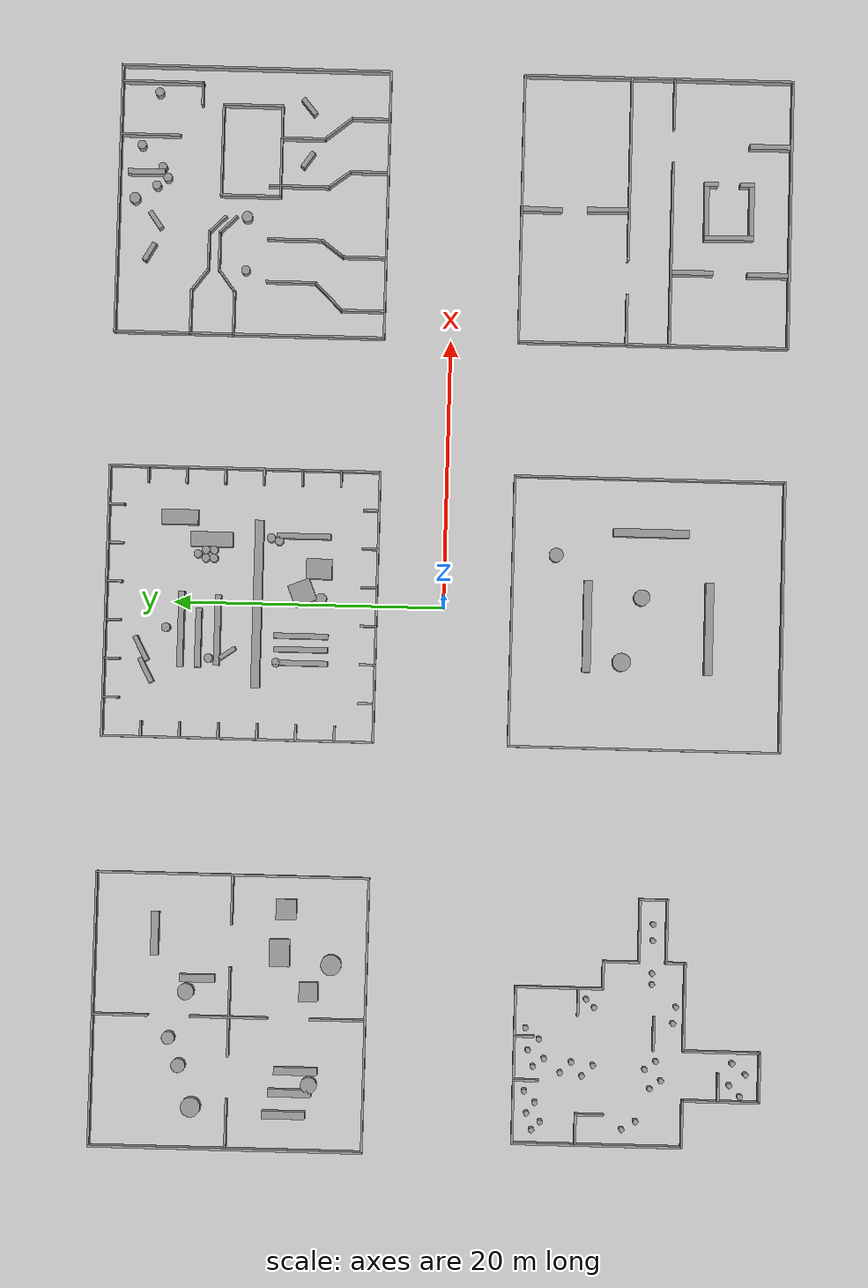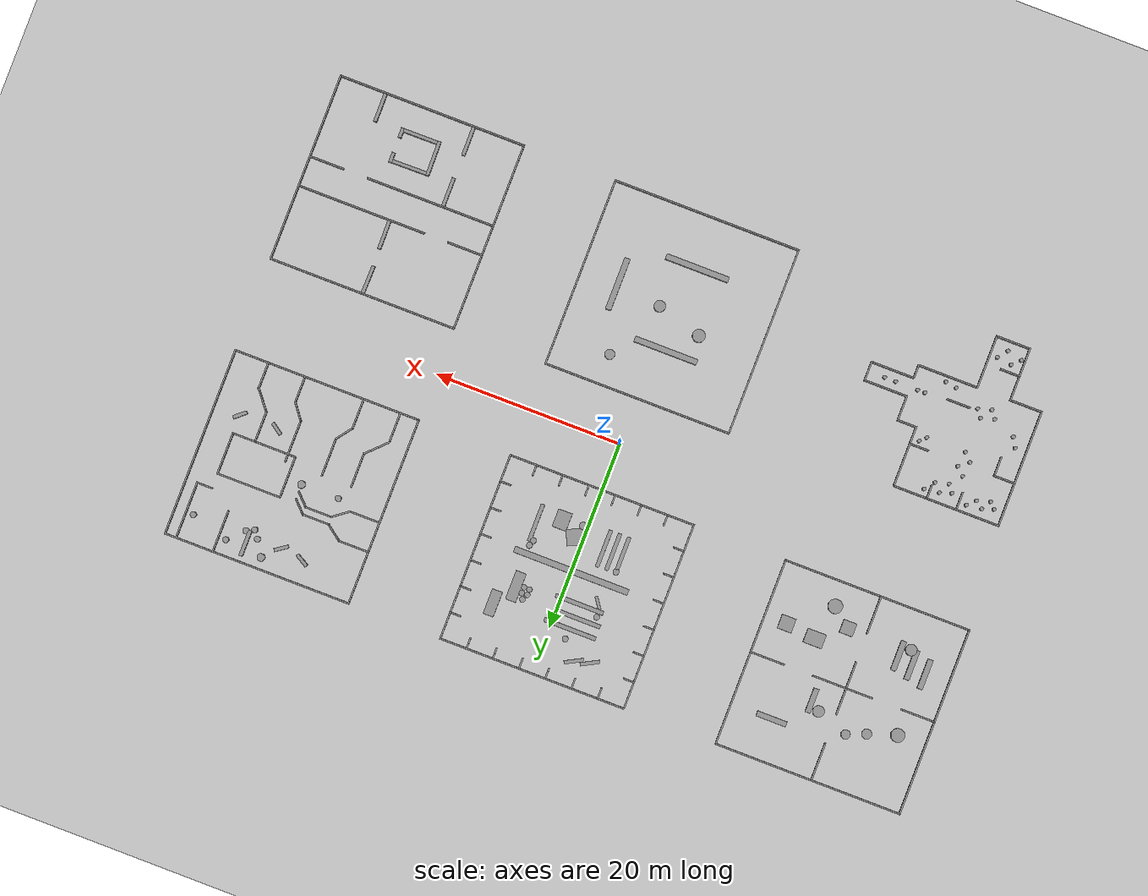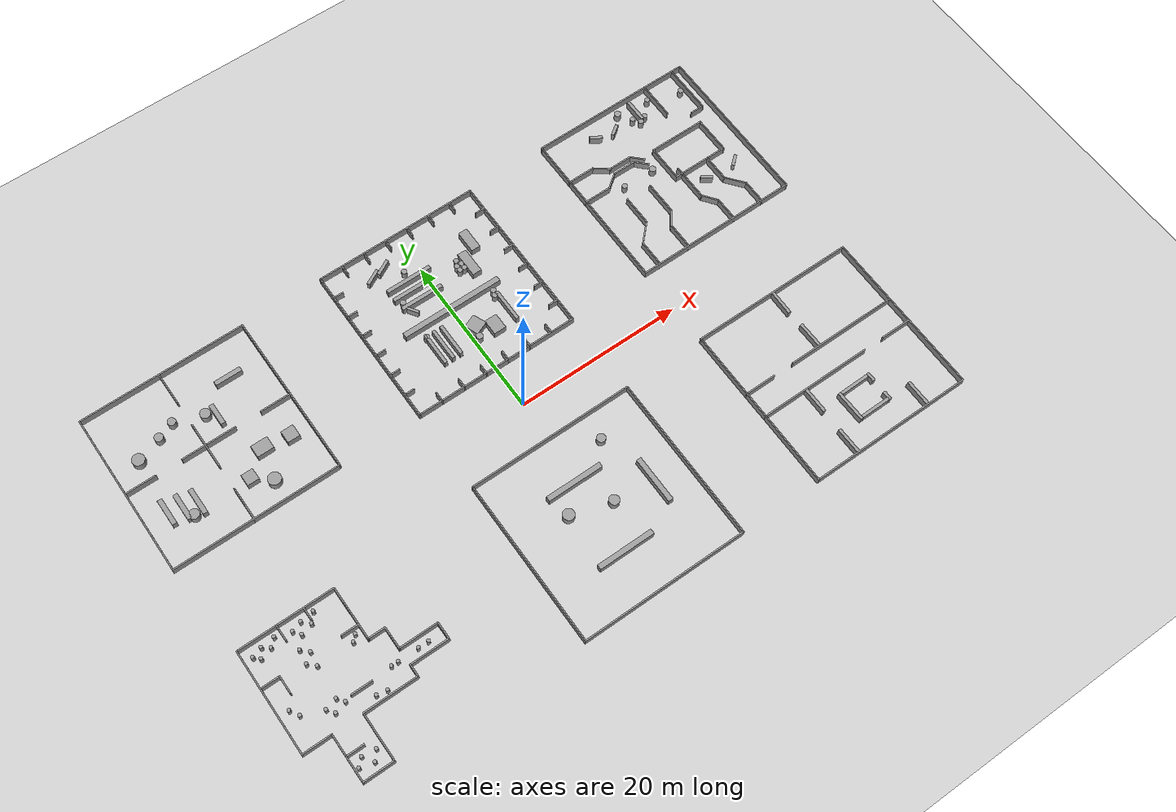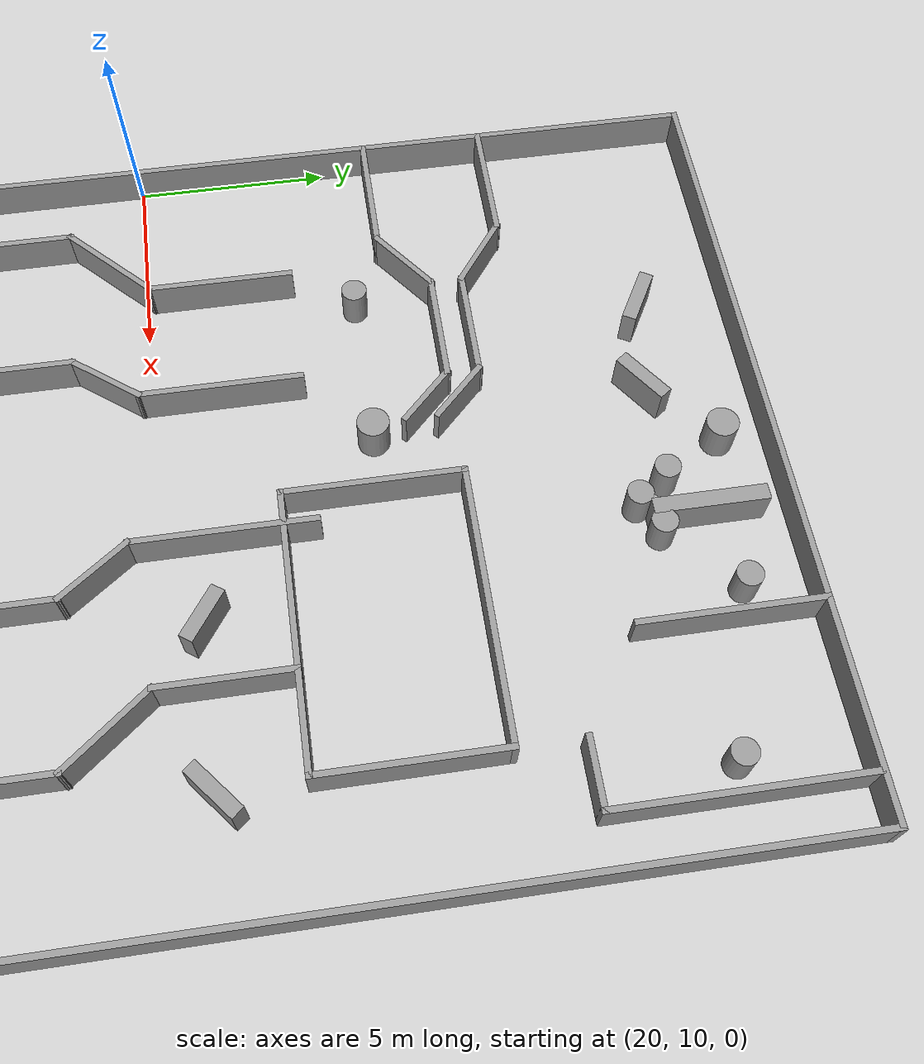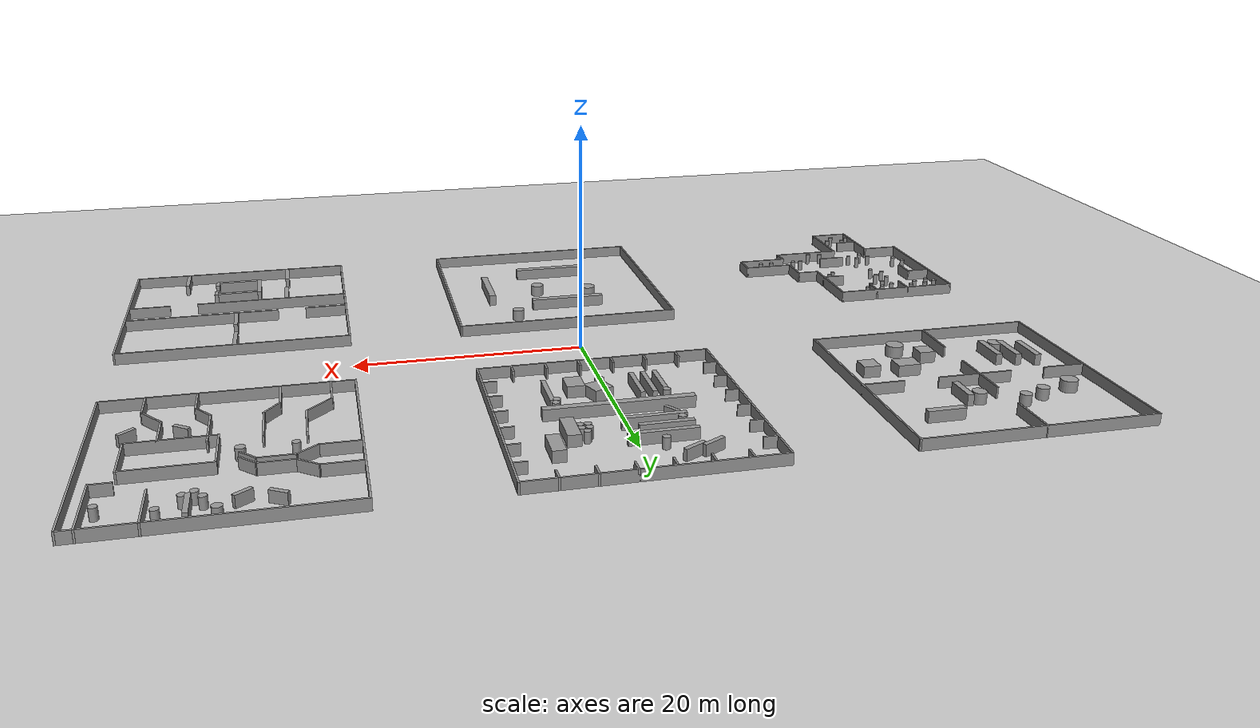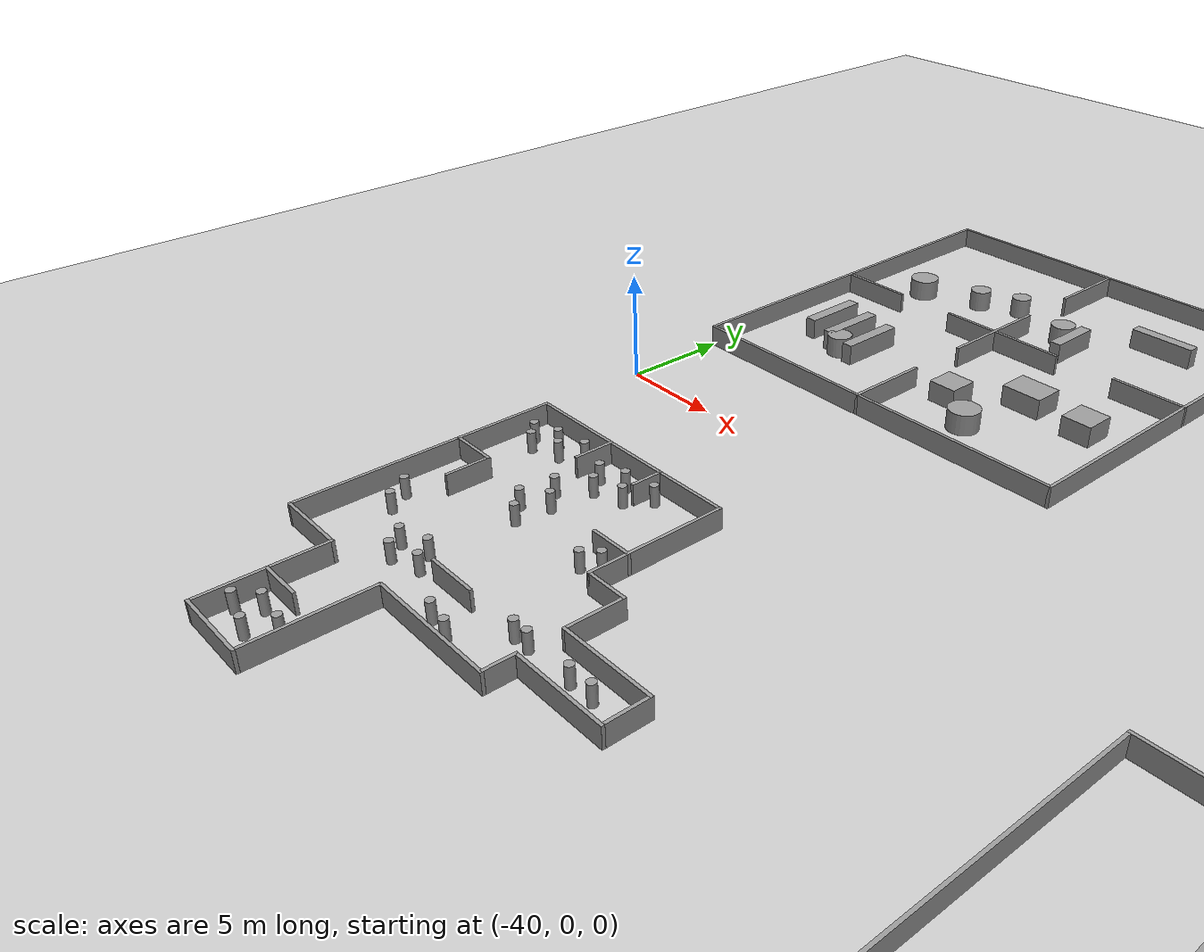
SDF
<?xml version='1.0' encoding='utf-8'?>
<sdf version="1.6"><world name="martha_training_islands"><include><uri>model://sun</uri></include>
    <include><uri>model://ground_plane</uri></include>

    <physics name="default_physics" default="true" type="ode">
      <max_step_size>0.001</max_step_size>
      <real_time_factor>1.0</real_time_factor>
      <real_time_update_rate>1000</real_time_update_rate>
    </physics>

    <scene>
      <ambient>0.4 0.4 0.4 1</ambient>
      <background>0.7 0.7 0.7 1</background>
      <shadows>false</shadows>
    </scene>

    <plugin name="gazebo_ros_state" filename="libgazebo_ros_state.so"><ros><namespace>/gazebo</namespace></ros><update_rate>100.0</update_rate></plugin><model name="four_rooms__four_rooms_obstacles">
      <pose>-30 15 0 0 0 0</pose><static>true</static>
      <link name="body">
      <collision name="col_0">
        <pose>0.0000 -10.0000 0.5000 0 0 0.00000</pose>
        <geometry>
          <box><size>20.1500 0.1500 1.0000</size></box>
        </geometry>
      </collision>
      <visual name="vis_0">
        <pose>0.0000 -10.0000 0.5000 0 0 0.00000</pose>
        <geometry>
          <box><size>20.1500 0.1500 1.0000</size></box>
        </geometry>
        <material>
          <script>
            <uri>file://media/materials/scripts/gazebo.material</uri>
            <name>Gazebo/Grey</name>
          </script>
        </material>
      </visual>
      <collision name="col_1">
        <pose>10.0000 0.0000 0.5000 0 0 1.57080</pose>
        <geometry>
          <box><size>20.1500 0.1500 1.0000</size></box>
        </geometry>
      </collision>
      <visual name="vis_1">
        <pose>10.0000 0.0000 0.5000 0 0 1.57080</pose>
        <geometry>
          <box><size>20.1500 0.1500 1.0000</size></box>
        </geometry>
        <material>
          <script>
            <uri>file://media/materials/scripts/gazebo.material</uri>
            <name>Gazebo/Grey</name>
          </script>
        </material>
      </visual>
      <collision name="col_2">
        <pose>0.0000 10.0000 0.5000 0 0 3.14159</pose>
        <geometry>
          <box><size>20.1500 0.1500 1.0000</size></box>
        </geometry>
      </collision>
      <visual name="vis_2">
        <pose>0.0000 10.0000 0.5000 0 0 3.14159</pose>
        <geometry>
          <box><size>20.1500 0.1500 1.0000</size></box>
        </geometry>
        <material>
          <script>
            <uri>file://media/materials/scripts/gazebo.material</uri>
            <name>Gazebo/Grey</name>
          </script>
        </material>
      </visual>
      <collision name="col_3">
        <pose>-10.0000 0.0000 0.5000 0 0 -1.57080</pose>
        <geometry>
          <box><size>20.1500 0.1500 1.0000</size></box>
        </geometry>
      </collision>
      <visual name="vis_3">
        <pose>-10.0000 0.0000 0.5000 0 0 -1.57080</pose>
        <geometry>
          <box><size>20.1500 0.1500 1.0000</size></box>
        </geometry>
        <material>
          <script>
            <uri>file://media/materials/scripts/gazebo.material</uri>
            <name>Gazebo/Grey</name>
          </script>
        </material>
      </visual>
      <collision name="col_4">
        <pose>-0.4000 -8.0000 0.5000 0 0 1.57080</pose>
        <geometry>
          <box><size>4.1500 0.1500 1.0000</size></box>
        </geometry>
      </collision>
      <visual name="vis_4">
        <pose>-0.4000 -8.0000 0.5000 0 0 1.57080</pose>
        <geometry>
          <box><size>4.1500 0.1500 1.0000</size></box>
        </geometry>
        <material>
          <script>
            <uri>file://media/materials/scripts/gazebo.material</uri>
            <name>Gazebo/Grey</name>
          </script>
        </material>
      </visual>
      <collision name="col_5">
        <pose>-0.4000 0.0000 0.5000 0 0 1.57080</pose>
        <geometry>
          <box><size>5.7500 0.1500 1.0000</size></box>
        </geometry>
      </collision>
      <visual name="vis_5">
        <pose>-0.4000 0.0000 0.5000 0 0 1.57080</pose>
        <geometry>
          <box><size>5.7500 0.1500 1.0000</size></box>
        </geometry>
        <material>
          <script>
            <uri>file://media/materials/scripts/gazebo.material</uri>
            <name>Gazebo/Grey</name>
          </script>
        </material>
      </visual>
      <collision name="col_6">
        <pose>-0.4000 8.0000 0.5000 0 0 1.57080</pose>
        <geometry>
          <box><size>4.1500 0.1500 1.0000</size></box>
        </geometry>
      </collision>
      <visual name="vis_6">
        <pose>-0.4000 8.0000 0.5000 0 0 1.57080</pose>
        <geometry>
          <box><size>4.1500 0.1500 1.0000</size></box>
        </geometry>
        <material>
          <script>
            <uri>file://media/materials/scripts/gazebo.material</uri>
            <name>Gazebo/Grey</name>
          </script>
        </material>
      </visual>
      <collision name="col_7">
        <pose>-8.2000 0.0000 0.5000 0 0 0.00000</pose>
        <geometry>
          <box><size>3.7500 0.1500 1.0000</size></box>
        </geometry>
      </collision>
      <visual name="vis_7">
        <pose>-8.2000 0.0000 0.5000 0 0 0.00000</pose>
        <geometry>
          <box><size>3.7500 0.1500 1.0000</size></box>
        </geometry>
        <material>
          <script>
            <uri>file://media/materials/scripts/gazebo.material</uri>
            <name>Gazebo/Grey</name>
          </script>
        </material>
      </visual>
      <collision name="col_8">
        <pose>0.0000 0.0000 0.5000 0 0 0.00000</pose>
        <geometry>
          <box><size>6.5500 0.1500 1.0000</size></box>
        </geometry>
      </collision>
      <visual name="vis_8">
        <pose>0.0000 0.0000 0.5000 0 0 0.00000</pose>
        <geometry>
          <box><size>6.5500 0.1500 1.0000</size></box>
        </geometry>
        <material>
          <script>
            <uri>file://media/materials/scripts/gazebo.material</uri>
            <name>Gazebo/Grey</name>
          </script>
        </material>
      </visual>
      <collision name="col_9">
        <pose>8.2000 0.0000 0.5000 0 0 0.00000</pose>
        <geometry>
          <box><size>3.7500 0.1500 1.0000</size></box>
        </geometry>
      </collision>
      <visual name="vis_9">
        <pose>8.2000 0.0000 0.5000 0 0 0.00000</pose>
        <geometry>
          <box><size>3.7500 0.1500 1.0000</size></box>
        </geometry>
        <material>
          <script>
            <uri>file://media/materials/scripts/gazebo.material</uri>
            <name>Gazebo/Grey</name>
          </script>
        </material>
      </visual>
      <collision name="col_10">
        <pose>5.6000 5.6000 0.5000 0 0 0.00000</pose>
        <geometry>
          <box><size>3.2000 0.5600 1.0000</size></box>
        </geometry>
      </collision>
      <visual name="vis_10">
        <pose>5.6000 5.6000 0.5000 0 0 0.00000</pose>
        <geometry>
          <box><size>3.2000 0.5600 1.0000</size></box>
        </geometry>
        <material>
          <script>
            <uri>file://media/materials/scripts/gazebo.material</uri>
            <name>Gazebo/Grey</name>
          </script>
        </material>
      </visual>
      <collision name="col_11">
        <pose>4.4000 -3.6000 0.5000 0 0 0.00000</pose>
        <geometry>
          <box><size>2.0000 1.5000 1.0000</size></box>
        </geometry>
      </collision>
      <visual name="vis_11">
        <pose>4.4000 -3.6000 0.5000 0 0 0.00000</pose>
        <geometry>
          <box><size>2.0000 1.5000 1.0000</size></box>
        </geometry>
        <material>
          <script>
            <uri>file://media/materials/scripts/gazebo.material</uri>
            <name>Gazebo/Grey</name>
          </script>
        </material>
      </visual>
      <collision name="col_12">
        <pose>1.6000 -5.8000 0.5000 0 0 0.00000</pose>
        <geometry>
          <box><size>1.4000 1.4000 1.0000</size></box>
        </geometry>
      </collision>
      <visual name="vis_12">
        <pose>1.6000 -5.8000 0.5000 0 0 0.00000</pose>
        <geometry>
          <box><size>1.4000 1.4000 1.0000</size></box>
        </geometry>
        <material>
          <script>
            <uri>file://media/materials/scripts/gazebo.material</uri>
            <name>Gazebo/Grey</name>
          </script>
        </material>
      </visual>
      <collision name="col_13">
        <pose>-7.4000 -4.2000 0.5000 0 0 0.00000</pose>
        <geometry>
          <box><size>0.5600 3.2000 1.0000</size></box>
        </geometry>
      </collision>
      <visual name="vis_13">
        <pose>-7.4000 -4.2000 0.5000 0 0 0.00000</pose>
        <geometry>
          <box><size>0.5600 3.2000 1.0000</size></box>
        </geometry>
        <material>
          <script>
            <uri>file://media/materials/scripts/gazebo.material</uri>
            <name>Gazebo/Grey</name>
          </script>
        </material>
      </visual>
      <collision name="col_14">
        <pose>-5.8000 -4.6000 0.5000 0 0 0.00000</pose>
        <geometry>
          <box><size>0.5600 3.2000 1.0000</size></box>
        </geometry>
      </collision>
      <visual name="vis_14">
        <pose>-5.8000 -4.6000 0.5000 0 0 0.00000</pose>
        <geometry>
          <box><size>0.5600 3.2000 1.0000</size></box>
        </geometry>
        <material>
          <script>
            <uri>file://media/materials/scripts/gazebo.material</uri>
            <name>Gazebo/Grey</name>
          </script>
        </material>
      </visual>
      <collision name="col_15">
        <pose>-4.2000 -5.0000 0.5000 0 0 0.00000</pose>
        <geometry>
          <box><size>0.5600 3.2000 1.0000</size></box>
        </geometry>
      </collision>
      <visual name="vis_15">
        <pose>-4.2000 -5.0000 0.5000 0 0 0.00000</pose>
        <geometry>
          <box><size>0.5600 3.2000 1.0000</size></box>
        </geometry>
        <material>
          <script>
            <uri>file://media/materials/scripts/gazebo.material</uri>
            <name>Gazebo/Grey</name>
          </script>
        </material>
      </visual>
      <collision name="col_16">
        <pose>2.4000 2.4000 0.5000 0 0 0.00000</pose>
        <geometry>
          <box><size>0.5600 2.6000 1.0000</size></box>
        </geometry>
      </collision>
      <visual name="vis_16">
        <pose>2.4000 2.4000 0.5000 0 0 0.00000</pose>
        <geometry>
          <box><size>0.5600 2.6000 1.0000</size></box>
        </geometry>
        <material>
          <script>
            <uri>file://media/materials/scripts/gazebo.material</uri>
            <name>Gazebo/Grey</name>
          </script>
        </material>
      </visual>
      <collision name="col_17">
        <pose>7.6000 -4.0000 0.5000 0 0 0.00000</pose>
        <geometry>
          <box><size>1.5000 1.5000 1.0000</size></box>
        </geometry>
      </collision>
      <visual name="vis_17">
        <pose>7.6000 -4.0000 0.5000 0 0 0.00000</pose>
        <geometry>
          <box><size>1.5000 1.5000 1.0000</size></box>
        </geometry>
        <material>
          <script>
            <uri>file://media/materials/scripts/gazebo.material</uri>
            <name>Gazebo/Grey</name>
          </script>
        </material>
      </visual>
      <collision name="col_18">
        <pose>-7.0000 2.6000 0.5000 0 0 0.00000</pose>
        <geometry>
          <cylinder><radius>0.7200</radius><length>1.0000</length></cylinder>
        </geometry>
      </collision>
      <visual name="vis_18">
        <pose>-7.0000 2.6000 0.5000 0 0 0.00000</pose>
        <geometry>
          <cylinder><radius>0.7200</radius><length>1.0000</length></cylinder>
        </geometry>
        <material>
          <script>
            <uri>file://media/materials/scripts/gazebo.material</uri>
            <name>Gazebo/Grey</name>
          </script>
        </material>
      </visual>
      <collision name="col_19">
        <pose>-4.0000 3.6000 0.5000 0 0 0.00000</pose>
        <geometry>
          <cylinder><radius>0.5200</radius><length>1.0000</length></cylinder>
        </geometry>
      </collision>
      <visual name="vis_19">
        <pose>-4.0000 3.6000 0.5000 0 0 0.00000</pose>
        <geometry>
          <cylinder><radius>0.5200</radius><length>1.0000</length></cylinder>
        </geometry>
        <material>
          <script>
            <uri>file://media/materials/scripts/gazebo.material</uri>
            <name>Gazebo/Grey</name>
          </script>
        </material>
      </visual>
      <collision name="col_20">
        <pose>-2.0000 4.4000 0.5000 0 0 0.00000</pose>
        <geometry>
          <cylinder><radius>0.4800</radius><length>1.0000</length></cylinder>
        </geometry>
      </collision>
      <visual name="vis_20">
        <pose>-2.0000 4.4000 0.5000 0 0 0.00000</pose>
        <geometry>
          <cylinder><radius>0.4800</radius><length>1.0000</length></cylinder>
        </geometry>
        <material>
          <script>
            <uri>file://media/materials/scripts/gazebo.material</uri>
            <name>Gazebo/Grey</name>
          </script>
        </material>
      </visual>
      <collision name="col_21">
        <pose>1.4000 3.2000 0.5000 0 0 0.00000</pose>
        <geometry>
          <cylinder><radius>0.6000</radius><length>1.0000</length></cylinder>
        </geometry>
      </collision>
      <visual name="vis_21">
        <pose>1.4000 3.2000 0.5000 0 0 0.00000</pose>
        <geometry>
          <cylinder><radius>0.6000</radius><length>1.0000</length></cylinder>
        </geometry>
        <material>
          <script>
            <uri>file://media/materials/scripts/gazebo.material</uri>
            <name>Gazebo/Grey</name>
          </script>
        </material>
      </visual>
      <collision name="col_22">
        <pose>3.6000 -7.4000 0.5000 0 0 0.00000</pose>
        <geometry>
          <cylinder><radius>0.7600</radius><length>1.0000</length></cylinder>
        </geometry>
      </collision>
      <visual name="vis_22">
        <pose>3.6000 -7.4000 0.5000 0 0 0.00000</pose>
        <geometry>
          <cylinder><radius>0.7600</radius><length>1.0000</length></cylinder>
        </geometry>
        <material>
          <script>
            <uri>file://media/materials/scripts/gazebo.material</uri>
            <name>Gazebo/Grey</name>
          </script>
        </material>
      </visual>
      <collision name="col_23">
        <pose>-5.2000 -6.0000 0.5000 0 0 0.00000</pose>
        <geometry>
          <cylinder><radius>0.6000</radius><length>1.0000</length></cylinder>
        </geometry>
      </collision>
      <visual name="vis_23">
        <pose>-5.2000 -6.0000 0.5000 0 0 0.00000</pose>
        <geometry>
          <cylinder><radius>0.6000</radius><length>1.0000</length></cylinder>
        </geometry>
        <material>
          <script>
            <uri>file://media/materials/scripts/gazebo.material</uri>
            <name>Gazebo/Grey</name>
          </script>
        </material>
      </visual>
      </link>
    </model>

  <model name="hall__hall_obstacles">
      <pose>0 15 0 0 0 0</pose><static>true</static>
      <link name="body">
      <collision name="col_0">
        <pose>0.0000 -10.0000 0.5000 0 0 0.00000</pose>
        <geometry>
          <box><size>20.1500 0.1500 1.0000</size></box>
        </geometry>
      </collision>
      <visual name="vis_0">
        <pose>0.0000 -10.0000 0.5000 0 0 0.00000</pose>
        <geometry>
          <box><size>20.1500 0.1500 1.0000</size></box>
        </geometry>
        <material>
          <script>
            <uri>file://media/materials/scripts/gazebo.material</uri>
            <name>Gazebo/Grey</name>
          </script>
        </material>
      </visual>
      <collision name="col_1">
        <pose>10.0000 0.0000 0.5000 0 0 1.57080</pose>
        <geometry>
          <box><size>20.1500 0.1500 1.0000</size></box>
        </geometry>
      </collision>
      <visual name="vis_1">
        <pose>10.0000 0.0000 0.5000 0 0 1.57080</pose>
        <geometry>
          <box><size>20.1500 0.1500 1.0000</size></box>
        </geometry>
        <material>
          <script>
            <uri>file://media/materials/scripts/gazebo.material</uri>
            <name>Gazebo/Grey</name>
          </script>
        </material>
      </visual>
      <collision name="col_2">
        <pose>0.0000 10.0000 0.5000 0 0 3.14159</pose>
        <geometry>
          <box><size>20.1500 0.1500 1.0000</size></box>
        </geometry>
      </collision>
      <visual name="vis_2">
        <pose>0.0000 10.0000 0.5000 0 0 3.14159</pose>
        <geometry>
          <box><size>20.1500 0.1500 1.0000</size></box>
        </geometry>
        <material>
          <script>
            <uri>file://media/materials/scripts/gazebo.material</uri>
            <name>Gazebo/Grey</name>
          </script>
        </material>
      </visual>
      <collision name="col_3">
        <pose>-10.0000 0.0000 0.5000 0 0 -1.57080</pose>
        <geometry>
          <box><size>20.1500 0.1500 1.0000</size></box>
        </geometry>
      </collision>
      <visual name="vis_3">
        <pose>-10.0000 0.0000 0.5000 0 0 -1.57080</pose>
        <geometry>
          <box><size>20.1500 0.1500 1.0000</size></box>
        </geometry>
        <material>
          <script>
            <uri>file://media/materials/scripts/gazebo.material</uri>
            <name>Gazebo/Grey</name>
          </script>
        </material>
      </visual>
      <collision name="col_4">
        <pose>-7.1429 -9.4500 0.5000 0 0 1.57080</pose>
        <geometry>
          <box><size>1.2500 0.1500 1.0000</size></box>
        </geometry>
      </collision>
      <visual name="vis_4">
        <pose>-7.1429 -9.4500 0.5000 0 0 1.57080</pose>
        <geometry>
          <box><size>1.2500 0.1500 1.0000</size></box>
        </geometry>
        <material>
          <script>
            <uri>file://media/materials/scripts/gazebo.material</uri>
            <name>Gazebo/Grey</name>
          </script>
        </material>
      </visual>
      <collision name="col_5">
        <pose>-7.1429 9.4500 0.5000 0 0 -1.57080</pose>
        <geometry>
          <box><size>1.2500 0.1500 1.0000</size></box>
        </geometry>
      </collision>
      <visual name="vis_5">
        <pose>-7.1429 9.4500 0.5000 0 0 -1.57080</pose>
        <geometry>
          <box><size>1.2500 0.1500 1.0000</size></box>
        </geometry>
        <material>
          <script>
            <uri>file://media/materials/scripts/gazebo.material</uri>
            <name>Gazebo/Grey</name>
          </script>
        </material>
      </visual>
      <collision name="col_6">
        <pose>-9.4500 -7.1429 0.5000 0 0 0.00000</pose>
        <geometry>
          <box><size>1.2500 0.1500 1.0000</size></box>
        </geometry>
      </collision>
      <visual name="vis_6">
        <pose>-9.4500 -7.1429 0.5000 0 0 0.00000</pose>
        <geometry>
          <box><size>1.2500 0.1500 1.0000</size></box>
        </geometry>
        <material>
          <script>
            <uri>file://media/materials/scripts/gazebo.material</uri>
            <name>Gazebo/Grey</name>
          </script>
        </material>
      </visual>
      <collision name="col_7">
        <pose>9.4500 -7.1429 0.5000 0 0 3.14159</pose>
        <geometry>
          <box><size>1.2500 0.1500 1.0000</size></box>
        </geometry>
      </collision>
      <visual name="vis_7">
        <pose>9.4500 -7.1429 0.5000 0 0 3.14159</pose>
        <geometry>
          <box><size>1.2500 0.1500 1.0000</size></box>
        </geometry>
        <material>
          <script>
            <uri>file://media/materials/scripts/gazebo.material</uri>
            <name>Gazebo/Grey</name>
          </script>
        </material>
      </visual>
      <collision name="col_8">
        <pose>-4.2857 -9.4500 0.5000 0 0 1.57080</pose>
        <geometry>
          <box><size>1.2500 0.1500 1.0000</size></box>
        </geometry>
      </collision>
      <visual name="vis_8">
        <pose>-4.2857 -9.4500 0.5000 0 0 1.57080</pose>
        <geometry>
          <box><size>1.2500 0.1500 1.0000</size></box>
        </geometry>
        <material>
          <script>
            <uri>file://media/materials/scripts/gazebo.material</uri>
            <name>Gazebo/Grey</name>
          </script>
        </material>
      </visual>
      <collision name="col_9">
        <pose>-4.2857 9.4500 0.5000 0 0 -1.57080</pose>
        <geometry>
          <box><size>1.2500 0.1500 1.0000</size></box>
        </geometry>
      </collision>
      <visual name="vis_9">
        <pose>-4.2857 9.4500 0.5000 0 0 -1.57080</pose>
        <geometry>
          <box><size>1.2500 0.1500 1.0000</size></box>
        </geometry>
        <material>
          <script>
            <uri>file://media/materials/scripts/gazebo.material</uri>
            <name>Gazebo/Grey</name>
          </script>
        </material>
      </visual>
      <collision name="col_10">
        <pose>-9.4500 -4.2857 0.5000 0 0 0.00000</pose>
        <geometry>
          <box><size>1.2500 0.1500 1.0000</size></box>
        </geometry>
      </collision>
      <visual name="vis_10">
        <pose>-9.4500 -4.2857 0.5000 0 0 0.00000</pose>
        <geometry>
          <box><size>1.2500 0.1500 1.0000</size></box>
        </geometry>
        <material>
          <script>
            <uri>file://media/materials/scripts/gazebo.material</uri>
            <name>Gazebo/Grey</name>
          </script>
        </material>
      </visual>
      <collision name="col_11">
        <pose>9.4500 -4.2857 0.5000 0 0 3.14159</pose>
        <geometry>
          <box><size>1.2500 0.1500 1.0000</size></box>
        </geometry>
      </collision>
      <visual name="vis_11">
        <pose>9.4500 -4.2857 0.5000 0 0 3.14159</pose>
        <geometry>
          <box><size>1.2500 0.1500 1.0000</size></box>
        </geometry>
        <material>
          <script>
            <uri>file://media/materials/scripts/gazebo.material</uri>
            <name>Gazebo/Grey</name>
          </script>
        </material>
      </visual>
      <collision name="col_12">
        <pose>-1.4286 -9.4500 0.5000 0 0 1.57080</pose>
        <geometry>
          <box><size>1.2500 0.1500 1.0000</size></box>
        </geometry>
      </collision>
      <visual name="vis_12">
        <pose>-1.4286 -9.4500 0.5000 0 0 1.57080</pose>
        <geometry>
          <box><size>1.2500 0.1500 1.0000</size></box>
        </geometry>
        <material>
          <script>
            <uri>file://media/materials/scripts/gazebo.material</uri>
            <name>Gazebo/Grey</name>
          </script>
        </material>
      </visual>
      <collision name="col_13">
        <pose>-1.4286 9.4500 0.5000 0 0 -1.57080</pose>
        <geometry>
          <box><size>1.2500 0.1500 1.0000</size></box>
        </geometry>
      </collision>
      <visual name="vis_13">
        <pose>-1.4286 9.4500 0.5000 0 0 -1.57080</pose>
        <geometry>
          <box><size>1.2500 0.1500 1.0000</size></box>
        </geometry>
        <material>
          <script>
            <uri>file://media/materials/scripts/gazebo.material</uri>
            <name>Gazebo/Grey</name>
          </script>
        </material>
      </visual>
      <collision name="col_14">
        <pose>-9.4500 -1.4286 0.5000 0 0 0.00000</pose>
        <geometry>
          <box><size>1.2500 0.1500 1.0000</size></box>
        </geometry>
      </collision>
      <visual name="vis_14">
        <pose>-9.4500 -1.4286 0.5000 0 0 0.00000</pose>
        <geometry>
          <box><size>1.2500 0.1500 1.0000</size></box>
        </geometry>
        <material>
          <script>
            <uri>file://media/materials/scripts/gazebo.material</uri>
            <name>Gazebo/Grey</name>
          </script>
        </material>
      </visual>
      <collision name="col_15">
        <pose>9.4500 -1.4286 0.5000 0 0 3.14159</pose>
        <geometry>
          <box><size>1.2500 0.1500 1.0000</size></box>
        </geometry>
      </collision>
      <visual name="vis_15">
        <pose>9.4500 -1.4286 0.5000 0 0 3.14159</pose>
        <geometry>
          <box><size>1.2500 0.1500 1.0000</size></box>
        </geometry>
        <material>
          <script>
            <uri>file://media/materials/scripts/gazebo.material</uri>
            <name>Gazebo/Grey</name>
          </script>
        </material>
      </visual>
      <collision name="col_16">
        <pose>1.4286 -9.4500 0.5000 0 0 1.57080</pose>
        <geometry>
          <box><size>1.2500 0.1500 1.0000</size></box>
        </geometry>
      </collision>
      <visual name="vis_16">
        <pose>1.4286 -9.4500 0.5000 0 0 1.57080</pose>
        <geometry>
          <box><size>1.2500 0.1500 1.0000</size></box>
        </geometry>
        <material>
          <script>
            <uri>file://media/materials/scripts/gazebo.material</uri>
            <name>Gazebo/Grey</name>
          </script>
        </material>
      </visual>
      <collision name="col_17">
        <pose>1.4286 9.4500 0.5000 0 0 -1.57080</pose>
        <geometry>
          <box><size>1.2500 0.1500 1.0000</size></box>
        </geometry>
      </collision>
      <visual name="vis_17">
        <pose>1.4286 9.4500 0.5000 0 0 -1.57080</pose>
        <geometry>
          <box><size>1.2500 0.1500 1.0000</size></box>
        </geometry>
        <material>
          <script>
            <uri>file://media/materials/scripts/gazebo.material</uri>
            <name>Gazebo/Grey</name>
          </script>
        </material>
      </visual>
      <collision name="col_18">
        <pose>-9.4500 1.4286 0.5000 0 0 0.00000</pose>
        <geometry>
          <box><size>1.2500 0.1500 1.0000</size></box>
        </geometry>
      </collision>
      <visual name="vis_18">
        <pose>-9.4500 1.4286 0.5000 0 0 0.00000</pose>
        <geometry>
          <box><size>1.2500 0.1500 1.0000</size></box>
        </geometry>
        <material>
          <script>
            <uri>file://media/materials/scripts/gazebo.material</uri>
            <name>Gazebo/Grey</name>
          </script>
        </material>
      </visual>
      <collision name="col_19">
        <pose>9.4500 1.4286 0.5000 0 0 3.14159</pose>
        <geometry>
          <box><size>1.2500 0.1500 1.0000</size></box>
        </geometry>
      </collision>
      <visual name="vis_19">
        <pose>9.4500 1.4286 0.5000 0 0 3.14159</pose>
        <geometry>
          <box><size>1.2500 0.1500 1.0000</size></box>
        </geometry>
        <material>
          <script>
            <uri>file://media/materials/scripts/gazebo.material</uri>
            <name>Gazebo/Grey</name>
          </script>
        </material>
      </visual>
      <collision name="col_20">
        <pose>4.2857 -9.4500 0.5000 0 0 1.57080</pose>
        <geometry>
          <box><size>1.2500 0.1500 1.0000</size></box>
        </geometry>
      </collision>
      <visual name="vis_20">
        <pose>4.2857 -9.4500 0.5000 0 0 1.57080</pose>
        <geometry>
          <box><size>1.2500 0.1500 1.0000</size></box>
        </geometry>
        <material>
          <script>
            <uri>file://media/materials/scripts/gazebo.material</uri>
            <name>Gazebo/Grey</name>
          </script>
        </material>
      </visual>
      <collision name="col_21">
        <pose>4.2857 9.4500 0.5000 0 0 -1.57080</pose>
        <geometry>
          <box><size>1.2500 0.1500 1.0000</size></box>
        </geometry>
      </collision>
      <visual name="vis_21">
        <pose>4.2857 9.4500 0.5000 0 0 -1.57080</pose>
        <geometry>
          <box><size>1.2500 0.1500 1.0000</size></box>
        </geometry>
        <material>
          <script>
            <uri>file://media/materials/scripts/gazebo.material</uri>
            <name>Gazebo/Grey</name>
          </script>
        </material>
      </visual>
      <collision name="col_22">
        <pose>-9.4500 4.2857 0.5000 0 0 0.00000</pose>
        <geometry>
          <box><size>1.2500 0.1500 1.0000</size></box>
        </geometry>
      </collision>
      <visual name="vis_22">
        <pose>-9.4500 4.2857 0.5000 0 0 0.00000</pose>
        <geometry>
          <box><size>1.2500 0.1500 1.0000</size></box>
        </geometry>
        <material>
          <script>
            <uri>file://media/materials/scripts/gazebo.material</uri>
            <name>Gazebo/Grey</name>
          </script>
        </material>
      </visual>
      <collision name="col_23">
        <pose>9.4500 4.2857 0.5000 0 0 3.14159</pose>
        <geometry>
          <box><size>1.2500 0.1500 1.0000</size></box>
        </geometry>
      </collision>
      <visual name="vis_23">
        <pose>9.4500 4.2857 0.5000 0 0 3.14159</pose>
        <geometry>
          <box><size>1.2500 0.1500 1.0000</size></box>
        </geometry>
        <material>
          <script>
            <uri>file://media/materials/scripts/gazebo.material</uri>
            <name>Gazebo/Grey</name>
          </script>
        </material>
      </visual>
      <collision name="col_24">
        <pose>7.1429 -9.4500 0.5000 0 0 1.57080</pose>
        <geometry>
          <box><size>1.2500 0.1500 1.0000</size></box>
        </geometry>
      </collision>
      <visual name="vis_24">
        <pose>7.1429 -9.4500 0.5000 0 0 1.57080</pose>
        <geometry>
          <box><size>1.2500 0.1500 1.0000</size></box>
        </geometry>
        <material>
          <script>
            <uri>file://media/materials/scripts/gazebo.material</uri>
            <name>Gazebo/Grey</name>
          </script>
        </material>
      </visual>
      <collision name="col_25">
        <pose>7.1429 9.4500 0.5000 0 0 -1.57080</pose>
        <geometry>
          <box><size>1.2500 0.1500 1.0000</size></box>
        </geometry>
      </collision>
      <visual name="vis_25">
        <pose>7.1429 9.4500 0.5000 0 0 -1.57080</pose>
        <geometry>
          <box><size>1.2500 0.1500 1.0000</size></box>
        </geometry>
        <material>
          <script>
            <uri>file://media/materials/scripts/gazebo.material</uri>
            <name>Gazebo/Grey</name>
          </script>
        </material>
      </visual>
      <collision name="col_26">
        <pose>-9.4500 7.1429 0.5000 0 0 0.00000</pose>
        <geometry>
          <box><size>1.2500 0.1500 1.0000</size></box>
        </geometry>
      </collision>
      <visual name="vis_26">
        <pose>-9.4500 7.1429 0.5000 0 0 0.00000</pose>
        <geometry>
          <box><size>1.2500 0.1500 1.0000</size></box>
        </geometry>
        <material>
          <script>
            <uri>file://media/materials/scripts/gazebo.material</uri>
            <name>Gazebo/Grey</name>
          </script>
        </material>
      </visual>
      <collision name="col_27">
        <pose>9.4500 7.1429 0.5000 0 0 3.14159</pose>
        <geometry>
          <box><size>1.2500 0.1500 1.0000</size></box>
        </geometry>
      </collision>
      <visual name="vis_27">
        <pose>9.4500 7.1429 0.5000 0 0 3.14159</pose>
        <geometry>
          <box><size>1.2500 0.1500 1.0000</size></box>
        </geometry>
        <material>
          <script>
            <uri>file://media/materials/scripts/gazebo.material</uri>
            <name>Gazebo/Grey</name>
          </script>
        </material>
      </visual>
      <collision name="col_28">
        <pose>0.0000 -1.2000 0.5000 0 0 0.00000</pose>
        <geometry>
          <box><size>12.4000 0.6400 1.0000</size></box>
        </geometry>
      </collision>
      <visual name="vis_28">
        <pose>0.0000 -1.2000 0.5000 0 0 0.00000</pose>
        <geometry>
          <box><size>12.4000 0.6400 1.0000</size></box>
        </geometry>
        <material>
          <script>
            <uri>file://media/materials/scripts/gazebo.material</uri>
            <name>Gazebo/Grey</name>
          </script>
        </material>
      </visual>
      <collision name="col_29">
        <pose>-2.0000 4.4000 0.5000 0 0 0.00000</pose>
        <geometry>
          <box><size>5.6000 0.4400 1.0000</size></box>
        </geometry>
      </collision>
      <visual name="vis_29">
        <pose>-2.0000 4.4000 0.5000 0 0 0.00000</pose>
        <geometry>
          <box><size>5.6000 0.4400 1.0000</size></box>
        </geometry>
        <material>
          <script>
            <uri>file://media/materials/scripts/gazebo.material</uri>
            <name>Gazebo/Grey</name>
          </script>
        </material>
      </visual>
      <collision name="col_30">
        <pose>-2.6000 3.1000 0.5000 0 0 0.00000</pose>
        <geometry>
          <box><size>4.4000 0.4400 1.0000</size></box>
        </geometry>
      </collision>
      <visual name="vis_30">
        <pose>-2.6000 3.1000 0.5000 0 0 0.00000</pose>
        <geometry>
          <box><size>4.4000 0.4400 1.0000</size></box>
        </geometry>
        <material>
          <script>
            <uri>file://media/materials/scripts/gazebo.material</uri>
            <name>Gazebo/Grey</name>
          </script>
        </material>
      </visual>
      <collision name="col_31">
        <pose>-2.0000 1.7000 0.5000 0 0 0.00000</pose>
        <geometry>
          <box><size>5.2000 0.4400 1.0000</size></box>
        </geometry>
      </collision>
      <visual name="vis_31">
        <pose>-2.0000 1.7000 0.5000 0 0 0.00000</pose>
        <geometry>
          <box><size>5.2000 0.4400 1.0000</size></box>
        </geometry>
        <material>
          <script>
            <uri>file://media/materials/scripts/gazebo.material</uri>
            <name>Gazebo/Grey</name>
          </script>
        </material>
      </visual>
      <collision name="col_32">
        <pose>-5.1000 6.9000 0.5000 0 0 0.48869</pose>
        <geometry>
          <box><size>2.0000 0.3600 1.0000</size></box>
        </geometry>
      </collision>
      <visual name="vis_32">
        <pose>-5.1000 6.9000 0.5000 0 0 0.48869</pose>
        <geometry>
          <box><size>2.0000 0.3600 1.0000</size></box>
        </geometry>
        <material>
          <script>
            <uri>file://media/materials/scripts/gazebo.material</uri>
            <name>Gazebo/Grey</name>
          </script>
        </material>
      </visual>
      <collision name="col_33">
        <pose>-3.5000 7.3000 0.5000 0 0 0.48869</pose>
        <geometry>
          <box><size>2.0000 0.3600 1.0000</size></box>
        </geometry>
      </collision>
      <visual name="vis_33">
        <pose>-3.5000 7.3000 0.5000 0 0 0.48869</pose>
        <geometry>
          <box><size>2.0000 0.3600 1.0000</size></box>
        </geometry>
        <material>
          <script>
            <uri>file://media/materials/scripts/gazebo.material</uri>
            <name>Gazebo/Grey</name>
          </script>
        </material>
      </visual>
      <collision name="col_34">
        <pose>-3.7000 0.9000 0.5000 0 0 -0.95993</pose>
        <geometry>
          <box><size>1.4000 0.3200 1.0000</size></box>
        </geometry>
      </collision>
      <visual name="vis_34">
        <pose>-3.7000 0.9000 0.5000 0 0 -0.95993</pose>
        <geometry>
          <box><size>1.4000 0.3200 1.0000</size></box>
        </geometry>
        <material>
          <script>
            <uri>file://media/materials/scripts/gazebo.material</uri>
            <name>Gazebo/Grey</name>
          </script>
        </material>
      </visual>
      <collision name="col_35">
        <pose>-4.3000 -4.5000 0.5000 0 0 0.00000</pose>
        <geometry>
          <box><size>0.4000 4.0000 1.0000</size></box>
        </geometry>
      </collision>
      <visual name="vis_35">
        <pose>-4.3000 -4.5000 0.5000 0 0 0.00000</pose>
        <geometry>
          <box><size>0.4000 4.0000 1.0000</size></box>
        </geometry>
        <material>
          <script>
            <uri>file://media/materials/scripts/gazebo.material</uri>
            <name>Gazebo/Grey</name>
          </script>
        </material>
      </visual>
      <collision name="col_36">
        <pose>-3.3000 -4.5000 0.5000 0 0 0.00000</pose>
        <geometry>
          <box><size>0.4000 4.0000 1.0000</size></box>
        </geometry>
      </collision>
      <visual name="vis_36">
        <pose>-3.3000 -4.5000 0.5000 0 0 0.00000</pose>
        <geometry>
          <box><size>0.4000 4.0000 1.0000</size></box>
        </geometry>
        <material>
          <script>
            <uri>file://media/materials/scripts/gazebo.material</uri>
            <name>Gazebo/Grey</name>
          </script>
        </material>
      </visual>
      <collision name="col_37">
        <pose>-2.3000 -4.5000 0.5000 0 0 0.00000</pose>
        <geometry>
          <box><size>0.4000 4.0000 1.0000</size></box>
        </geometry>
      </collision>
      <visual name="vis_37">
        <pose>-2.3000 -4.5000 0.5000 0 0 0.00000</pose>
        <geometry>
          <box><size>0.4000 4.0000 1.0000</size></box>
        </geometry>
        <material>
          <script>
            <uri>file://media/materials/scripts/gazebo.material</uri>
            <name>Gazebo/Grey</name>
          </script>
        </material>
      </visual>
      <collision name="col_38">
        <pose>5.1000 -4.5000 0.5000 0 0 0.00000</pose>
        <geometry>
          <box><size>0.4000 4.0000 1.0000</size></box>
        </geometry>
      </collision>
      <visual name="vis_38">
        <pose>5.1000 -4.5000 0.5000 0 0 0.00000</pose>
        <geometry>
          <box><size>0.4000 4.0000 1.0000</size></box>
        </geometry>
        <material>
          <script>
            <uri>file://media/materials/scripts/gazebo.material</uri>
            <name>Gazebo/Grey</name>
          </script>
        </material>
      </visual>
      <collision name="col_39">
        <pose>0.9000 -4.5000 0.5000 0 0 0.38397</pose>
        <geometry>
          <box><size>1.7000 1.7000 1.0000</size></box>
        </geometry>
      </collision>
      <visual name="vis_39">
        <pose>0.9000 -4.5000 0.5000 0 0 0.38397</pose>
        <geometry>
          <box><size>1.7000 1.7000 1.0000</size></box>
        </geometry>
        <material>
          <script>
            <uri>file://media/materials/scripts/gazebo.material</uri>
            <name>Gazebo/Grey</name>
          </script>
        </material>
      </visual>
      <collision name="col_40">
        <pose>2.7000 -5.7000 0.5000 0 0 0.00000</pose>
        <geometry>
          <box><size>1.5000 1.9000 1.0000</size></box>
        </geometry>
      </collision>
      <visual name="vis_40">
        <pose>2.7000 -5.7000 0.5000 0 0 0.00000</pose>
        <geometry>
          <box><size>1.5000 1.9000 1.0000</size></box>
        </geometry>
        <material>
          <script>
            <uri>file://media/materials/scripts/gazebo.material</uri>
            <name>Gazebo/Grey</name>
          </script>
        </material>
      </visual>
      <collision name="col_41">
        <pose>4.7000 2.3000 0.5000 0 0 0.00000</pose>
        <geometry>
          <box><size>1.1000 3.1000 1.0000</size></box>
        </geometry>
      </collision>
      <visual name="vis_41">
        <pose>4.7000 2.3000 0.5000 0 0 0.00000</pose>
        <geometry>
          <box><size>1.1000 3.1000 1.0000</size></box>
        </geometry>
        <material>
          <script>
            <uri>file://media/materials/scripts/gazebo.material</uri>
            <name>Gazebo/Grey</name>
          </script>
        </material>
      </visual>
      <collision name="col_42">
        <pose>6.3000 4.7000 0.5000 0 0 0.00000</pose>
        <geometry>
          <box><size>1.1000 2.7000 1.0000</size></box>
        </geometry>
      </collision>
      <visual name="vis_42">
        <pose>6.3000 4.7000 0.5000 0 0 0.00000</pose>
        <geometry>
          <box><size>1.1000 2.7000 1.0000</size></box>
        </geometry>
        <material>
          <script>
            <uri>file://media/materials/scripts/gazebo.material</uri>
            <name>Gazebo/Grey</name>
          </script>
        </material>
      </visual>
      <collision name="col_43">
        <pose>-1.9000 5.5000 0.5000 0 0 0.00000</pose>
        <geometry>
          <cylinder><radius>0.3200</radius><length>1.0000</length></cylinder>
        </geometry>
      </collision>
      <visual name="vis_43">
        <pose>-1.9000 5.5000 0.5000 0 0 0.00000</pose>
        <geometry>
          <cylinder><radius>0.3200</radius><length>1.0000</length></cylinder>
        </geometry>
        <material>
          <script>
            <uri>file://media/materials/scripts/gazebo.material</uri>
            <name>Gazebo/Grey</name>
          </script>
        </material>
      </visual>
      <collision name="col_44">
        <pose>-4.1000 2.3000 0.5000 0 0 0.00000</pose>
        <geometry>
          <cylinder><radius>0.3200</radius><length>1.0000</length></cylinder>
        </geometry>
      </collision>
      <visual name="vis_44">
        <pose>-4.1000 2.3000 0.5000 0 0 0.00000</pose>
        <geometry>
          <cylinder><radius>0.3200</radius><length>1.0000</length></cylinder>
        </geometry>
        <material>
          <script>
            <uri>file://media/materials/scripts/gazebo.material</uri>
            <name>Gazebo/Grey</name>
          </script>
        </material>
      </visual>
      <collision name="col_45">
        <pose>-4.3000 -2.7000 0.5000 0 0 0.00000</pose>
        <geometry>
          <cylinder><radius>0.3200</radius><length>1.0000</length></cylinder>
        </geometry>
      </collision>
      <visual name="vis_45">
        <pose>-4.3000 -2.7000 0.5000 0 0 0.00000</pose>
        <geometry>
          <cylinder><radius>0.3200</radius><length>1.0000</length></cylinder>
        </geometry>
        <material>
          <script>
            <uri>file://media/materials/scripts/gazebo.material</uri>
            <name>Gazebo/Grey</name>
          </script>
        </material>
      </visual>
      <collision name="col_46">
        <pose>0.5000 -5.9000 0.5000 0 0 0.00000</pose>
        <geometry>
          <cylinder><radius>0.4000</radius><length>1.0000</length></cylinder>
        </geometry>
      </collision>
      <visual name="vis_46">
        <pose>0.5000 -5.9000 0.5000 0 0 0.00000</pose>
        <geometry>
          <cylinder><radius>0.4000</radius><length>1.0000</length></cylinder>
        </geometry>
        <material>
          <script>
            <uri>file://media/materials/scripts/gazebo.material</uri>
            <name>Gazebo/Grey</name>
          </script>
        </material>
      </visual>
      <collision name="col_47">
        <pose>4.7000 -2.7000 0.5000 0 0 0.00000</pose>
        <geometry>
          <cylinder><radius>0.3200</radius><length>1.0000</length></cylinder>
        </geometry>
      </collision>
      <visual name="vis_47">
        <pose>4.7000 -2.7000 0.5000 0 0 0.00000</pose>
        <geometry>
          <cylinder><radius>0.3200</radius><length>1.0000</length></cylinder>
        </geometry>
        <material>
          <script>
            <uri>file://media/materials/scripts/gazebo.material</uri>
            <name>Gazebo/Grey</name>
          </script>
        </material>
      </visual>
      <collision name="col_48">
        <pose>4.9000 -2.1000 0.5000 0 0 0.00000</pose>
        <geometry>
          <cylinder><radius>0.3200</radius><length>1.0000</length></cylinder>
        </geometry>
      </collision>
      <visual name="vis_48">
        <pose>4.9000 -2.1000 0.5000 0 0 0.00000</pose>
        <geometry>
          <cylinder><radius>0.3200</radius><length>1.0000</length></cylinder>
        </geometry>
        <material>
          <script>
            <uri>file://media/materials/scripts/gazebo.material</uri>
            <name>Gazebo/Grey</name>
          </script>
        </material>
      </visual>
      <collision name="col_49">
        <pose>3.3000 2.1000 0.5000 0 0 0.00000</pose>
        <geometry>
          <cylinder><radius>0.3000</radius><length>1.0000</length></cylinder>
        </geometry>
      </collision>
      <visual name="vis_49">
        <pose>3.3000 2.1000 0.5000 0 0 0.00000</pose>
        <geometry>
          <cylinder><radius>0.3000</radius><length>1.0000</length></cylinder>
        </geometry>
        <material>
          <script>
            <uri>file://media/materials/scripts/gazebo.material</uri>
            <name>Gazebo/Grey</name>
          </script>
        </material>
      </visual>
      <collision name="col_50">
        <pose>3.9000 2.1000 0.5000 0 0 0.00000</pose>
        <geometry>
          <cylinder><radius>0.3000</radius><length>1.0000</length></cylinder>
        </geometry>
      </collision>
      <visual name="vis_50">
        <pose>3.9000 2.1000 0.5000 0 0 0.00000</pose>
        <geometry>
          <cylinder><radius>0.3000</radius><length>1.0000</length></cylinder>
        </geometry>
        <material>
          <script>
            <uri>file://media/materials/scripts/gazebo.material</uri>
            <name>Gazebo/Grey</name>
          </script>
        </material>
      </visual>
      <collision name="col_51">
        <pose>3.3000 2.7000 0.5000 0 0 0.00000</pose>
        <geometry>
          <cylinder><radius>0.3000</radius><length>1.0000</length></cylinder>
        </geometry>
      </collision>
      <visual name="vis_51">
        <pose>3.3000 2.7000 0.5000 0 0 0.00000</pose>
        <geometry>
          <cylinder><radius>0.3000</radius><length>1.0000</length></cylinder>
        </geometry>
        <material>
          <script>
            <uri>file://media/materials/scripts/gazebo.material</uri>
            <name>Gazebo/Grey</name>
          </script>
        </material>
      </visual>
      <collision name="col_52">
        <pose>3.9000 2.7000 0.5000 0 0 0.00000</pose>
        <geometry>
          <cylinder><radius>0.3000</radius><length>1.0000</length></cylinder>
        </geometry>
      </collision>
      <visual name="vis_52">
        <pose>3.9000 2.7000 0.5000 0 0 0.00000</pose>
        <geometry>
          <cylinder><radius>0.3000</radius><length>1.0000</length></cylinder>
        </geometry>
        <material>
          <script>
            <uri>file://media/materials/scripts/gazebo.material</uri>
            <name>Gazebo/Grey</name>
          </script>
        </material>
      </visual>
      <collision name="col_53">
        <pose>3.6000 3.3000 0.5000 0 0 0.00000</pose>
        <geometry>
          <cylinder><radius>0.3000</radius><length>1.0000</length></cylinder>
        </geometry>
      </collision>
      <visual name="vis_53">
        <pose>3.6000 3.3000 0.5000 0 0 0.00000</pose>
        <geometry>
          <cylinder><radius>0.3000</radius><length>1.0000</length></cylinder>
        </geometry>
        <material>
          <script>
            <uri>file://media/materials/scripts/gazebo.material</uri>
            <name>Gazebo/Grey</name>
          </script>
        </material>
      </visual>
      </link>
    </model>

  <model name="multi__multi_obstacles">
      <pose>30 15 0 0 0 0</pose><static>true</static>
      <link name="body">
      <collision name="col_0">
        <pose>0.0000 -10.0000 0.5000 0 0 0.00000</pose>
        <geometry>
          <box><size>20.1500 0.1500 1.0000</size></box>
        </geometry>
      </collision>
      <visual name="vis_0">
        <pose>0.0000 -10.0000 0.5000 0 0 0.00000</pose>
        <geometry>
          <box><size>20.1500 0.1500 1.0000</size></box>
        </geometry>
        <material>
          <script>
            <uri>file://media/materials/scripts/gazebo.material</uri>
            <name>Gazebo/Grey</name>
          </script>
        </material>
      </visual>
      <collision name="col_1">
        <pose>10.0000 0.0000 0.5000 0 0 1.57080</pose>
        <geometry>
          <box><size>20.1500 0.1500 1.0000</size></box>
        </geometry>
      </collision>
      <visual name="vis_1">
        <pose>10.0000 0.0000 0.5000 0 0 1.57080</pose>
        <geometry>
          <box><size>20.1500 0.1500 1.0000</size></box>
        </geometry>
        <material>
          <script>
            <uri>file://media/materials/scripts/gazebo.material</uri>
            <name>Gazebo/Grey</name>
          </script>
        </material>
      </visual>
      <collision name="col_2">
        <pose>0.0000 10.0000 0.5000 0 0 3.14159</pose>
        <geometry>
          <box><size>20.1500 0.1500 1.0000</size></box>
        </geometry>
      </collision>
      <visual name="vis_2">
        <pose>0.0000 10.0000 0.5000 0 0 3.14159</pose>
        <geometry>
          <box><size>20.1500 0.1500 1.0000</size></box>
        </geometry>
        <material>
          <script>
            <uri>file://media/materials/scripts/gazebo.material</uri>
            <name>Gazebo/Grey</name>
          </script>
        </material>
      </visual>
      <collision name="col_3">
        <pose>-10.0000 0.0000 0.5000 0 0 -1.57080</pose>
        <geometry>
          <box><size>20.1500 0.1500 1.0000</size></box>
        </geometry>
      </collision>
      <visual name="vis_3">
        <pose>-10.0000 0.0000 0.5000 0 0 -1.57080</pose>
        <geometry>
          <box><size>20.1500 0.1500 1.0000</size></box>
        </geometry>
        <material>
          <script>
            <uri>file://media/materials/scripts/gazebo.material</uri>
            <name>Gazebo/Grey</name>
          </script>
        </material>
      </visual>
      <collision name="col_4">
        <pose>-8.4000 4.4000 0.5000 0 0 0.00000</pose>
        <geometry>
          <box><size>3.3500 0.1500 1.0000</size></box>
        </geometry>
      </collision>
      <visual name="vis_4">
        <pose>-8.4000 4.4000 0.5000 0 0 0.00000</pose>
        <geometry>
          <box><size>3.3500 0.1500 1.0000</size></box>
        </geometry>
        <material>
          <script>
            <uri>file://media/materials/scripts/gazebo.material</uri>
            <name>Gazebo/Grey</name>
          </script>
        </material>
      </visual>
      <collision name="col_5">
        <pose>-6.0000 3.8000 0.5000 0 0 -0.64350</pose>
        <geometry>
          <box><size>2.1500 0.1500 1.0000</size></box>
        </geometry>
      </collision>
      <visual name="vis_5">
        <pose>-6.0000 3.8000 0.5000 0 0 -0.64350</pose>
        <geometry>
          <box><size>2.1500 0.1500 1.0000</size></box>
        </geometry>
        <material>
          <script>
            <uri>file://media/materials/scripts/gazebo.material</uri>
            <name>Gazebo/Grey</name>
          </script>
        </material>
      </visual>
      <collision name="col_6">
        <pose>-3.8000 3.2000 0.5000 0 0 0.00000</pose>
        <geometry>
          <box><size>2.9500 0.1500 1.0000</size></box>
        </geometry>
      </collision>
      <visual name="vis_6">
        <pose>-3.8000 3.2000 0.5000 0 0 0.00000</pose>
        <geometry>
          <box><size>2.9500 0.1500 1.0000</size></box>
        </geometry>
        <material>
          <script>
            <uri>file://media/materials/scripts/gazebo.material</uri>
            <name>Gazebo/Grey</name>
          </script>
        </material>
      </visual>
      <collision name="col_7">
        <pose>-1.8000 2.6000 0.5000 0 0 -0.78540</pose>
        <geometry>
          <box><size>1.8471 0.1500 1.0000</size></box>
        </geometry>
      </collision>
      <visual name="vis_7">
        <pose>-1.8000 2.6000 0.5000 0 0 -0.78540</pose>
        <geometry>
          <box><size>1.8471 0.1500 1.0000</size></box>
        </geometry>
        <material>
          <script>
            <uri>file://media/materials/scripts/gazebo.material</uri>
            <name>Gazebo/Grey</name>
          </script>
        </material>
      </visual>
      <collision name="col_8">
        <pose>-8.4000 1.2000 0.5000 0 0 0.00000</pose>
        <geometry>
          <box><size>3.3500 0.1500 1.0000</size></box>
        </geometry>
      </collision>
      <visual name="vis_8">
        <pose>-8.4000 1.2000 0.5000 0 0 0.00000</pose>
        <geometry>
          <box><size>3.3500 0.1500 1.0000</size></box>
        </geometry>
        <material>
          <script>
            <uri>file://media/materials/scripts/gazebo.material</uri>
            <name>Gazebo/Grey</name>
          </script>
        </material>
      </visual>
      <collision name="col_9">
        <pose>-6.0000 1.8000 0.5000 0 0 0.64350</pose>
        <geometry>
          <box><size>2.1500 0.1500 1.0000</size></box>
        </geometry>
      </collision>
      <visual name="vis_9">
        <pose>-6.0000 1.8000 0.5000 0 0 0.64350</pose>
        <geometry>
          <box><size>2.1500 0.1500 1.0000</size></box>
        </geometry>
        <material>
          <script>
            <uri>file://media/materials/scripts/gazebo.material</uri>
            <name>Gazebo/Grey</name>
          </script>
        </material>
      </visual>
      <collision name="col_10">
        <pose>-3.8000 2.4000 0.5000 0 0 0.00000</pose>
        <geometry>
          <box><size>2.9500 0.1500 1.0000</size></box>
        </geometry>
      </collision>
      <visual name="vis_10">
        <pose>-3.8000 2.4000 0.5000 0 0 0.00000</pose>
        <geometry>
          <box><size>2.9500 0.1500 1.0000</size></box>
        </geometry>
        <material>
          <script>
            <uri>file://media/materials/scripts/gazebo.material</uri>
            <name>Gazebo/Grey</name>
          </script>
        </material>
      </visual>
      <collision name="col_11">
        <pose>-1.8000 1.8000 0.5000 0 0 -0.78540</pose>
        <geometry>
          <box><size>1.8471 0.1500 1.0000</size></box>
        </geometry>
      </collision>
      <visual name="vis_11">
        <pose>-1.8000 1.8000 0.5000 0 0 -0.78540</pose>
        <geometry>
          <box><size>1.8471 0.1500 1.0000</size></box>
        </geometry>
        <material>
          <script>
            <uri>file://media/materials/scripts/gazebo.material</uri>
            <name>Gazebo/Grey</name>
          </script>
        </material>
      </visual>
      <collision name="col_12">
        <pose>-8.0000 -8.4000 0.5000 0 0 1.57080</pose>
        <geometry>
          <box><size>3.3500 0.1500 1.0000</size></box>
        </geometry>
      </collision>
      <visual name="vis_12">
        <pose>-8.0000 -8.4000 0.5000 0 0 1.57080</pose>
        <geometry>
          <box><size>3.3500 0.1500 1.0000</size></box>
        </geometry>
        <material>
          <script>
            <uri>file://media/materials/scripts/gazebo.material</uri>
            <name>Gazebo/Grey</name>
          </script>
        </material>
      </visual>
      <collision name="col_13">
        <pose>-7.0000 -5.8000 0.5000 0 0 0.78540</pose>
        <geometry>
          <box><size>2.9784 0.1500 1.0000</size></box>
        </geometry>
      </collision>
      <visual name="vis_13">
        <pose>-7.0000 -5.8000 0.5000 0 0 0.78540</pose>
        <geometry>
          <box><size>2.9784 0.1500 1.0000</size></box>
        </geometry>
        <material>
          <script>
            <uri>file://media/materials/scripts/gazebo.material</uri>
            <name>Gazebo/Grey</name>
          </script>
        </material>
      </visual>
      <collision name="col_14">
        <pose>-6.0000 -3.0000 0.5000 0 0 1.57080</pose>
        <geometry>
          <box><size>3.7500 0.1500 1.0000</size></box>
        </geometry>
      </collision>
      <visual name="vis_14">
        <pose>-6.0000 -3.0000 0.5000 0 0 1.57080</pose>
        <geometry>
          <box><size>3.7500 0.1500 1.0000</size></box>
        </geometry>
        <material>
          <script>
            <uri>file://media/materials/scripts/gazebo.material</uri>
            <name>Gazebo/Grey</name>
          </script>
        </material>
      </visual>
      <collision name="col_15">
        <pose>-4.0000 -8.4000 0.5000 0 0 1.57080</pose>
        <geometry>
          <box><size>3.3500 0.1500 1.0000</size></box>
        </geometry>
      </collision>
      <visual name="vis_15">
        <pose>-4.0000 -8.4000 0.5000 0 0 1.57080</pose>
        <geometry>
          <box><size>3.3500 0.1500 1.0000</size></box>
        </geometry>
        <material>
          <script>
            <uri>file://media/materials/scripts/gazebo.material</uri>
            <name>Gazebo/Grey</name>
          </script>
        </material>
      </visual>
      <collision name="col_16">
        <pose>-3.4000 -6.0000 0.5000 0 0 0.92730</pose>
        <geometry>
          <box><size>2.1500 0.1500 1.0000</size></box>
        </geometry>
      </collision>
      <visual name="vis_16">
        <pose>-3.4000 -6.0000 0.5000 0 0 0.92730</pose>
        <geometry>
          <box><size>2.1500 0.1500 1.0000</size></box>
        </geometry>
        <material>
          <script>
            <uri>file://media/materials/scripts/gazebo.material</uri>
            <name>Gazebo/Grey</name>
          </script>
        </material>
      </visual>
      <collision name="col_17">
        <pose>-2.8000 -3.2000 0.5000 0 0 1.57080</pose>
        <geometry>
          <box><size>4.1500 0.1500 1.0000</size></box>
        </geometry>
      </collision>
      <visual name="vis_17">
        <pose>-2.8000 -3.2000 0.5000 0 0 1.57080</pose>
        <geometry>
          <box><size>4.1500 0.1500 1.0000</size></box>
        </geometry>
        <material>
          <script>
            <uri>file://media/materials/scripts/gazebo.material</uri>
            <name>Gazebo/Grey</name>
          </script>
        </material>
      </visual>
      <collision name="col_18">
        <pose>2.4000 -8.6000 0.5000 0 0 1.57080</pose>
        <geometry>
          <box><size>2.9500 0.1500 1.0000</size></box>
        </geometry>
      </collision>
      <visual name="vis_18">
        <pose>2.4000 -8.6000 0.5000 0 0 1.57080</pose>
        <geometry>
          <box><size>2.9500 0.1500 1.0000</size></box>
        </geometry>
        <material>
          <script>
            <uri>file://media/materials/scripts/gazebo.material</uri>
            <name>Gazebo/Grey</name>
          </script>
        </material>
      </visual>
      <collision name="col_19">
        <pose>1.8000 -6.4000 0.5000 0 0 2.21430</pose>
        <geometry>
          <box><size>2.1500 0.1500 1.0000</size></box>
        </geometry>
      </collision>
      <visual name="vis_19">
        <pose>1.8000 -6.4000 0.5000 0 0 2.21430</pose>
        <geometry>
          <box><size>2.1500 0.1500 1.0000</size></box>
        </geometry>
        <material>
          <script>
            <uri>file://media/materials/scripts/gazebo.material</uri>
            <name>Gazebo/Grey</name>
          </script>
        </material>
      </visual>
      <collision name="col_20">
        <pose>1.2000 -3.4000 0.5000 0 0 1.57080</pose>
        <geometry>
          <box><size>4.5500 0.1500 1.0000</size></box>
        </geometry>
      </collision>
      <visual name="vis_20">
        <pose>1.2000 -3.4000 0.5000 0 0 1.57080</pose>
        <geometry>
          <box><size>4.5500 0.1500 1.0000</size></box>
        </geometry>
        <material>
          <script>
            <uri>file://media/materials/scripts/gazebo.material</uri>
            <name>Gazebo/Grey</name>
          </script>
        </material>
      </visual>
      <collision name="col_21">
        <pose>6.4000 -8.6000 0.5000 0 0 1.57080</pose>
        <geometry>
          <box><size>2.9500 0.1500 1.0000</size></box>
        </geometry>
      </collision>
      <visual name="vis_21">
        <pose>6.4000 -8.6000 0.5000 0 0 1.57080</pose>
        <geometry>
          <box><size>2.9500 0.1500 1.0000</size></box>
        </geometry>
        <material>
          <script>
            <uri>file://media/materials/scripts/gazebo.material</uri>
            <name>Gazebo/Grey</name>
          </script>
        </material>
      </visual>
      <collision name="col_22">
        <pose>5.6000 -6.2000 0.5000 0 0 2.24554</pose>
        <geometry>
          <box><size>2.7112 0.1500 1.0000</size></box>
        </geometry>
      </collision>
      <visual name="vis_22">
        <pose>5.6000 -6.2000 0.5000 0 0 2.24554</pose>
        <geometry>
          <box><size>2.7112 0.1500 1.0000</size></box>
        </geometry>
        <material>
          <script>
            <uri>file://media/materials/scripts/gazebo.material</uri>
            <name>Gazebo/Grey</name>
          </script>
        </material>
      </visual>
      <collision name="col_23">
        <pose>4.8000 -3.6000 0.5000 0 0 1.57080</pose>
        <geometry>
          <box><size>3.3500 0.1500 1.0000</size></box>
        </geometry>
      </collision>
      <visual name="vis_23">
        <pose>4.8000 -3.6000 0.5000 0 0 1.57080</pose>
        <geometry>
          <box><size>3.3500 0.1500 1.0000</size></box>
        </geometry>
        <material>
          <script>
            <uri>file://media/materials/scripts/gazebo.material</uri>
            <name>Gazebo/Grey</name>
          </script>
        </material>
      </visual>
      <collision name="col_24">
        <pose>3.8000 -2.0000 0.5000 0 0 0.00000</pose>
        <geometry>
          <box><size>6.9500 0.1500 1.0000</size></box>
        </geometry>
      </collision>
      <visual name="vis_24">
        <pose>3.8000 -2.0000 0.5000 0 0 0.00000</pose>
        <geometry>
          <box><size>6.9500 0.1500 1.0000</size></box>
        </geometry>
        <material>
          <script>
            <uri>file://media/materials/scripts/gazebo.material</uri>
            <name>Gazebo/Grey</name>
          </script>
        </material>
      </visual>
      <collision name="col_25">
        <pose>7.2000 0.2000 0.5000 0 0 1.57080</pose>
        <geometry>
          <box><size>4.5500 0.1500 1.0000</size></box>
        </geometry>
      </collision>
      <visual name="vis_25">
        <pose>7.2000 0.2000 0.5000 0 0 1.57080</pose>
        <geometry>
          <box><size>4.5500 0.1500 1.0000</size></box>
        </geometry>
        <material>
          <script>
            <uri>file://media/materials/scripts/gazebo.material</uri>
            <name>Gazebo/Grey</name>
          </script>
        </material>
      </visual>
      <collision name="col_26">
        <pose>3.8000 2.4000 0.5000 0 0 3.14159</pose>
        <geometry>
          <box><size>6.9500 0.1500 1.0000</size></box>
        </geometry>
      </collision>
      <visual name="vis_26">
        <pose>3.8000 2.4000 0.5000 0 0 3.14159</pose>
        <geometry>
          <box><size>6.9500 0.1500 1.0000</size></box>
        </geometry>
        <material>
          <script>
            <uri>file://media/materials/scripts/gazebo.material</uri>
            <name>Gazebo/Grey</name>
          </script>
        </material>
      </visual>
      <collision name="col_27">
        <pose>0.4000 0.2000 0.5000 0 0 -1.57080</pose>
        <geometry>
          <box><size>4.5500 0.1500 1.0000</size></box>
        </geometry>
      </collision>
      <visual name="vis_27">
        <pose>0.4000 0.2000 0.5000 0 0 -1.57080</pose>
        <geometry>
          <box><size>4.5500 0.1500 1.0000</size></box>
        </geometry>
        <material>
          <script>
            <uri>file://media/materials/scripts/gazebo.material</uri>
            <name>Gazebo/Grey</name>
          </script>
        </material>
      </visual>
      <collision name="col_28">
        <pose>8.0000 4.0000 0.5000 0 0 0.00000</pose>
        <geometry>
          <box><size>1.7500 0.1500 1.0000</size></box>
        </geometry>
      </collision>
      <visual name="vis_28">
        <pose>8.0000 4.0000 0.5000 0 0 0.00000</pose>
        <geometry>
          <box><size>1.7500 0.1500 1.0000</size></box>
        </geometry>
        <material>
          <script>
            <uri>file://media/materials/scripts/gazebo.material</uri>
            <name>Gazebo/Grey</name>
          </script>
        </material>
      </visual>
      <collision name="col_29">
        <pose>8.8000 7.0000 0.5000 0 0 1.57080</pose>
        <geometry>
          <box><size>6.1500 0.1500 1.0000</size></box>
        </geometry>
      </collision>
      <visual name="vis_29">
        <pose>8.8000 7.0000 0.5000 0 0 1.57080</pose>
        <geometry>
          <box><size>6.1500 0.1500 1.0000</size></box>
        </geometry>
        <material>
          <script>
            <uri>file://media/materials/scripts/gazebo.material</uri>
            <name>Gazebo/Grey</name>
          </script>
        </material>
      </visual>
      <collision name="col_30">
        <pose>4.8000 7.8000 0.5000 0 0 1.57080</pose>
        <geometry>
          <box><size>4.5500 0.1500 1.0000</size></box>
        </geometry>
      </collision>
      <visual name="vis_30">
        <pose>4.8000 7.8000 0.5000 0 0 1.57080</pose>
        <geometry>
          <box><size>4.5500 0.1500 1.0000</size></box>
        </geometry>
        <material>
          <script>
            <uri>file://media/materials/scripts/gazebo.material</uri>
            <name>Gazebo/Grey</name>
          </script>
        </material>
      </visual>
      <collision name="col_31">
        <pose>2.0000 8.0000 0.5000 0 0 0.00000</pose>
        <geometry>
          <box><size>0.4000 2.8000 1.0000</size></box>
        </geometry>
      </collision>
      <visual name="vis_31">
        <pose>2.0000 8.0000 0.5000 0 0 0.00000</pose>
        <geometry>
          <box><size>0.4000 2.8000 1.0000</size></box>
        </geometry>
        <material>
          <script>
            <uri>file://media/materials/scripts/gazebo.material</uri>
            <name>Gazebo/Grey</name>
          </script>
        </material>
      </visual>
      <collision name="col_32">
        <pose>-1.6000 7.2000 0.5000 0 0 0.61087</pose>
        <geometry>
          <box><size>1.5000 0.3600 1.0000</size></box>
        </geometry>
      </collision>
      <visual name="vis_32">
        <pose>-1.6000 7.2000 0.5000 0 0 0.61087</pose>
        <geometry>
          <box><size>1.5000 0.3600 1.0000</size></box>
        </geometry>
        <material>
          <script>
            <uri>file://media/materials/scripts/gazebo.material</uri>
            <name>Gazebo/Grey</name>
          </script>
        </material>
      </visual>
      <collision name="col_33">
        <pose>-4.0000 7.6000 0.5000 0 0 -0.52360</pose>
        <geometry>
          <box><size>1.5000 0.3600 1.0000</size></box>
        </geometry>
      </collision>
      <visual name="vis_33">
        <pose>-4.0000 7.6000 0.5000 0 0 -0.52360</pose>
        <geometry>
          <box><size>1.5000 0.3600 1.0000</size></box>
        </geometry>
        <material>
          <script>
            <uri>file://media/materials/scripts/gazebo.material</uri>
            <name>Gazebo/Grey</name>
          </script>
        </material>
      </visual>
      <collision name="col_34">
        <pose>7.2000 -4.0000 0.5000 0 0 0.69813</pose>
        <geometry>
          <box><size>1.5000 0.3600 1.0000</size></box>
        </geometry>
      </collision>
      <visual name="vis_34">
        <pose>7.2000 -4.0000 0.5000 0 0 0.69813</pose>
        <geometry>
          <box><size>1.5000 0.3600 1.0000</size></box>
        </geometry>
        <material>
          <script>
            <uri>file://media/materials/scripts/gazebo.material</uri>
            <name>Gazebo/Grey</name>
          </script>
        </material>
      </visual>
      <collision name="col_35">
        <pose>3.2000 -4.0000 0.5000 0 0 -0.61087</pose>
        <geometry>
          <box><size>1.4000 0.3600 1.0000</size></box>
        </geometry>
      </collision>
      <visual name="vis_35">
        <pose>3.2000 -4.0000 0.5000 0 0 -0.61087</pose>
        <geometry>
          <box><size>1.4000 0.3600 1.0000</size></box>
        </geometry>
        <material>
          <script>
            <uri>file://media/materials/scripts/gazebo.material</uri>
            <name>Gazebo/Grey</name>
          </script>
        </material>
      </visual>
      <collision name="col_36">
        <pose>0.0000 8.8000 0.5000 0 0 0.00000</pose>
        <geometry>
          <cylinder><radius>0.4000</radius><length>1.0000</length></cylinder>
        </geometry>
      </collision>
      <visual name="vis_36">
        <pose>0.0000 8.8000 0.5000 0 0 0.00000</pose>
        <geometry>
          <cylinder><radius>0.4000</radius><length>1.0000</length></cylinder>
        </geometry>
        <material>
          <script>
            <uri>file://media/materials/scripts/gazebo.material</uri>
            <name>Gazebo/Grey</name>
          </script>
        </material>
      </visual>
      <collision name="col_37">
        <pose>1.0000 7.2000 0.5000 0 0 0.00000</pose>
        <geometry>
          <cylinder><radius>0.3200</radius><length>1.0000</length></cylinder>
        </geometry>
      </collision>
      <visual name="vis_37">
        <pose>1.0000 7.2000 0.5000 0 0 0.00000</pose>
        <geometry>
          <cylinder><radius>0.3200</radius><length>1.0000</length></cylinder>
        </geometry>
        <material>
          <script>
            <uri>file://media/materials/scripts/gazebo.material</uri>
            <name>Gazebo/Grey</name>
          </script>
        </material>
      </visual>
      <collision name="col_38">
        <pose>1.6000 6.4000 0.5000 0 0 0.00000</pose>
        <geometry>
          <cylinder><radius>0.3200</radius><length>1.0000</length></cylinder>
        </geometry>
      </collision>
      <visual name="vis_38">
        <pose>1.6000 6.4000 0.5000 0 0 0.00000</pose>
        <geometry>
          <cylinder><radius>0.3200</radius><length>1.0000</length></cylinder>
        </geometry>
        <material>
          <script>
            <uri>file://media/materials/scripts/gazebo.material</uri>
            <name>Gazebo/Grey</name>
          </script>
        </material>
      </visual>
      <collision name="col_39">
        <pose>2.4000 6.8000 0.5000 0 0 0.00000</pose>
        <geometry>
          <cylinder><radius>0.3200</radius><length>1.0000</length></cylinder>
        </geometry>
      </collision>
      <visual name="vis_39">
        <pose>2.4000 6.8000 0.5000 0 0 0.00000</pose>
        <geometry>
          <cylinder><radius>0.3200</radius><length>1.0000</length></cylinder>
        </geometry>
        <material>
          <script>
            <uri>file://media/materials/scripts/gazebo.material</uri>
            <name>Gazebo/Grey</name>
          </script>
        </material>
      </visual>
      <collision name="col_40">
        <pose>4.0000 8.4000 0.5000 0 0 0.00000</pose>
        <geometry>
          <cylinder><radius>0.3200</radius><length>1.0000</length></cylinder>
        </geometry>
      </collision>
      <visual name="vis_40">
        <pose>4.0000 8.4000 0.5000 0 0 0.00000</pose>
        <geometry>
          <cylinder><radius>0.3200</radius><length>1.0000</length></cylinder>
        </geometry>
        <material>
          <script>
            <uri>file://media/materials/scripts/gazebo.material</uri>
            <name>Gazebo/Grey</name>
          </script>
        </material>
      </visual>
      <collision name="col_41">
        <pose>-1.2000 0.4000 0.5000 0 0 0.00000</pose>
        <geometry>
          <cylinder><radius>0.4000</radius><length>1.0000</length></cylinder>
        </geometry>
      </collision>
      <visual name="vis_41">
        <pose>-1.2000 0.4000 0.5000 0 0 0.00000</pose>
        <geometry>
          <cylinder><radius>0.4000</radius><length>1.0000</length></cylinder>
        </geometry>
        <material>
          <script>
            <uri>file://media/materials/scripts/gazebo.material</uri>
            <name>Gazebo/Grey</name>
          </script>
        </material>
      </visual>
      <collision name="col_42">
        <pose>8.0000 7.2000 0.5000 0 0 0.00000</pose>
        <geometry>
          <cylinder><radius>0.3200</radius><length>1.0000</length></cylinder>
        </geometry>
      </collision>
      <visual name="vis_42">
        <pose>8.0000 7.2000 0.5000 0 0 0.00000</pose>
        <geometry>
          <cylinder><radius>0.3200</radius><length>1.0000</length></cylinder>
        </geometry>
        <material>
          <script>
            <uri>file://media/materials/scripts/gazebo.material</uri>
            <name>Gazebo/Grey</name>
          </script>
        </material>
      </visual>
      <collision name="col_43">
        <pose>-5.2000 0.4000 0.5000 0 0 0.00000</pose>
        <geometry>
          <cylinder><radius>0.3200</radius><length>1.0000</length></cylinder>
        </geometry>
      </collision>
      <visual name="vis_43">
        <pose>-5.2000 0.4000 0.5000 0 0 0.00000</pose>
        <geometry>
          <cylinder><radius>0.3200</radius><length>1.0000</length></cylinder>
        </geometry>
        <material>
          <script>
            <uri>file://media/materials/scripts/gazebo.material</uri>
            <name>Gazebo/Grey</name>
          </script>
        </material>
      </visual>
      </link>
    </model>

  <model name="roblab__roblab_obstacles">
      <pose>-30 -15 0 0 0 0</pose><static>true</static>
      <link name="body">
      <collision name="col_0">
        <pose>-3.3000 9.0000 0.5000 0 0 0.00000</pose>
        <geometry>
          <box><size>11.5500 0.1500 1.0000</size></box>
        </geometry>
      </collision>
      <visual name="vis_0">
        <pose>-3.3000 9.0000 0.5000 0 0 0.00000</pose>
        <geometry>
          <box><size>11.5500 0.1500 1.0000</size></box>
        </geometry>
        <material>
          <script>
            <uri>file://media/materials/scripts/gazebo.material</uri>
            <name>Gazebo/Grey</name>
          </script>
        </material>
      </visual>
      <collision name="col_1">
        <pose>2.4000 5.8000 0.5000 0 0 -1.57080</pose>
        <geometry>
          <box><size>6.5500 0.1500 1.0000</size></box>
        </geometry>
      </collision>
      <visual name="vis_1">
        <pose>2.4000 5.8000 0.5000 0 0 -1.57080</pose>
        <geometry>
          <box><size>6.5500 0.1500 1.0000</size></box>
        </geometry>
        <material>
          <script>
            <uri>file://media/materials/scripts/gazebo.material</uri>
            <name>Gazebo/Grey</name>
          </script>
        </material>
      </visual>
      <collision name="col_2">
        <pose>3.4000 2.6000 0.5000 0 0 0.00000</pose>
        <geometry>
          <box><size>2.1500 0.1500 1.0000</size></box>
        </geometry>
      </collision>
      <visual name="vis_2">
        <pose>3.4000 2.6000 0.5000 0 0 0.00000</pose>
        <geometry>
          <box><size>2.1500 0.1500 1.0000</size></box>
        </geometry>
        <material>
          <script>
            <uri>file://media/materials/scripts/gazebo.material</uri>
            <name>Gazebo/Grey</name>
          </script>
        </material>
      </visual>
      <collision name="col_3">
        <pose>4.4000 1.3000 0.5000 0 0 -1.57080</pose>
        <geometry>
          <box><size>2.7500 0.1500 1.0000</size></box>
        </geometry>
      </collision>
      <visual name="vis_3">
        <pose>4.4000 1.3000 0.5000 0 0 -1.57080</pose>
        <geometry>
          <box><size>2.7500 0.1500 1.0000</size></box>
        </geometry>
        <material>
          <script>
            <uri>file://media/materials/scripts/gazebo.material</uri>
            <name>Gazebo/Grey</name>
          </script>
        </material>
      </visual>
      <collision name="col_4">
        <pose>6.7000 0.0000 0.5000 0 0 0.00000</pose>
        <geometry>
          <box><size>4.7500 0.1500 1.0000</size></box>
        </geometry>
      </collision>
      <visual name="vis_4">
        <pose>6.7000 0.0000 0.5000 0 0 0.00000</pose>
        <geometry>
          <box><size>4.7500 0.1500 1.0000</size></box>
        </geometry>
        <material>
          <script>
            <uri>file://media/materials/scripts/gazebo.material</uri>
            <name>Gazebo/Grey</name>
          </script>
        </material>
      </visual>
      <collision name="col_5">
        <pose>9.0000 -1.0000 0.5000 0 0 -1.57080</pose>
        <geometry>
          <box><size>2.1500 0.1500 1.0000</size></box>
        </geometry>
      </collision>
      <visual name="vis_5">
        <pose>9.0000 -1.0000 0.5000 0 0 -1.57080</pose>
        <geometry>
          <box><size>2.1500 0.1500 1.0000</size></box>
        </geometry>
        <material>
          <script>
            <uri>file://media/materials/scripts/gazebo.material</uri>
            <name>Gazebo/Grey</name>
          </script>
        </material>
      </visual>
      <collision name="col_6">
        <pose>6.7000 -2.0000 0.5000 0 0 3.14159</pose>
        <geometry>
          <box><size>4.7500 0.1500 1.0000</size></box>
        </geometry>
      </collision>
      <visual name="vis_6">
        <pose>6.7000 -2.0000 0.5000 0 0 3.14159</pose>
        <geometry>
          <box><size>4.7500 0.1500 1.0000</size></box>
        </geometry>
        <material>
          <script>
            <uri>file://media/materials/scripts/gazebo.material</uri>
            <name>Gazebo/Grey</name>
          </script>
        </material>
      </visual>
      <collision name="col_7">
        <pose>4.4000 -2.7000 0.5000 0 0 -1.57080</pose>
        <geometry>
          <box><size>1.5500 0.1500 1.0000</size></box>
        </geometry>
      </collision>
      <visual name="vis_7">
        <pose>4.4000 -2.7000 0.5000 0 0 -1.57080</pose>
        <geometry>
          <box><size>1.5500 0.1500 1.0000</size></box>
        </geometry>
        <material>
          <script>
            <uri>file://media/materials/scripts/gazebo.material</uri>
            <name>Gazebo/Grey</name>
          </script>
        </material>
      </visual>
      <collision name="col_8">
        <pose>1.2000 -3.4000 0.5000 0 0 3.14159</pose>
        <geometry>
          <box><size>6.5500 0.1500 1.0000</size></box>
        </geometry>
      </collision>
      <visual name="vis_8">
        <pose>1.2000 -3.4000 0.5000 0 0 3.14159</pose>
        <geometry>
          <box><size>6.5500 0.1500 1.0000</size></box>
        </geometry>
        <material>
          <script>
            <uri>file://media/materials/scripts/gazebo.material</uri>
            <name>Gazebo/Grey</name>
          </script>
        </material>
      </visual>
      <collision name="col_9">
        <pose>-2.0000 -6.2000 0.5000 0 0 -1.57080</pose>
        <geometry>
          <box><size>5.7500 0.1500 1.0000</size></box>
        </geometry>
      </collision>
      <visual name="vis_9">
        <pose>-2.0000 -6.2000 0.5000 0 0 -1.57080</pose>
        <geometry>
          <box><size>5.7500 0.1500 1.0000</size></box>
        </geometry>
        <material>
          <script>
            <uri>file://media/materials/scripts/gazebo.material</uri>
            <name>Gazebo/Grey</name>
          </script>
        </material>
      </visual>
      <collision name="col_10">
        <pose>-3.8000 -9.0000 0.5000 0 0 3.14159</pose>
        <geometry>
          <box><size>3.7500 0.1500 1.0000</size></box>
        </geometry>
      </collision>
      <visual name="vis_10">
        <pose>-3.8000 -9.0000 0.5000 0 0 3.14159</pose>
        <geometry>
          <box><size>3.7500 0.1500 1.0000</size></box>
        </geometry>
        <material>
          <script>
            <uri>file://media/materials/scripts/gazebo.material</uri>
            <name>Gazebo/Grey</name>
          </script>
        </material>
      </visual>
      <collision name="col_11">
        <pose>-5.6000 -6.2000 0.5000 0 0 1.57080</pose>
        <geometry>
          <box><size>5.7500 0.1500 1.0000</size></box>
        </geometry>
      </collision>
      <visual name="vis_11">
        <pose>-5.6000 -6.2000 0.5000 0 0 1.57080</pose>
        <geometry>
          <box><size>5.7500 0.1500 1.0000</size></box>
        </geometry>
        <material>
          <script>
            <uri>file://media/materials/scripts/gazebo.material</uri>
            <name>Gazebo/Grey</name>
          </script>
        </material>
      </visual>
      <collision name="col_12">
        <pose>-7.3000 -3.4000 0.5000 0 0 3.14159</pose>
        <geometry>
          <box><size>3.5500 0.1500 1.0000</size></box>
        </geometry>
      </collision>
      <visual name="vis_12">
        <pose>-7.3000 -3.4000 0.5000 0 0 3.14159</pose>
        <geometry>
          <box><size>3.5500 0.1500 1.0000</size></box>
        </geometry>
        <material>
          <script>
            <uri>file://media/materials/scripts/gazebo.material</uri>
            <name>Gazebo/Grey</name>
          </script>
        </material>
      </visual>
      <collision name="col_13">
        <pose>-9.0000 2.8000 0.5000 0 0 1.57080</pose>
        <geometry>
          <box><size>12.5500 0.1500 1.0000</size></box>
        </geometry>
      </collision>
      <visual name="vis_13">
        <pose>-9.0000 2.8000 0.5000 0 0 1.57080</pose>
        <geometry>
          <box><size>12.5500 0.1500 1.0000</size></box>
        </geometry>
        <material>
          <script>
            <uri>file://media/materials/scripts/gazebo.material</uri>
            <name>Gazebo/Grey</name>
          </script>
        </material>
      </visual>
      <collision name="col_14">
        <pose>-7.9000 4.4000 0.5000 0 0 0.00000</pose>
        <geometry>
          <box><size>2.3500 0.1500 1.0000</size></box>
        </geometry>
      </collision>
      <visual name="vis_14">
        <pose>-7.9000 4.4000 0.5000 0 0 0.00000</pose>
        <geometry>
          <box><size>2.3500 0.1500 1.0000</size></box>
        </geometry>
        <material>
          <script>
            <uri>file://media/materials/scripts/gazebo.material</uri>
            <name>Gazebo/Grey</name>
          </script>
        </material>
      </visual>
      <collision name="col_15">
        <pose>-6.8000 3.4000 0.5000 0 0 -1.57080</pose>
        <geometry>
          <box><size>2.1500 0.1500 1.0000</size></box>
        </geometry>
      </collision>
      <visual name="vis_15">
        <pose>-6.8000 3.4000 0.5000 0 0 -1.57080</pose>
        <geometry>
          <box><size>2.1500 0.1500 1.0000</size></box>
        </geometry>
        <material>
          <script>
            <uri>file://media/materials/scripts/gazebo.material</uri>
            <name>Gazebo/Grey</name>
          </script>
        </material>
      </visual>
      <collision name="col_16">
        <pose>-4.4000 8.1000 0.5000 0 0 -1.57080</pose>
        <geometry>
          <box><size>1.9500 0.1500 1.0000</size></box>
        </geometry>
      </collision>
      <visual name="vis_16">
        <pose>-4.4000 8.1000 0.5000 0 0 -1.57080</pose>
        <geometry>
          <box><size>1.9500 0.1500 1.0000</size></box>
        </geometry>
        <material>
          <script>
            <uri>file://media/materials/scripts/gazebo.material</uri>
            <name>Gazebo/Grey</name>
          </script>
        </material>
      </visual>
      <collision name="col_17">
        <pose>-1.2000 8.3000 0.5000 0 0 -1.57080</pose>
        <geometry>
          <box><size>1.5500 0.1500 1.0000</size></box>
        </geometry>
      </collision>
      <visual name="vis_17">
        <pose>-1.2000 8.3000 0.5000 0 0 -1.57080</pose>
        <geometry>
          <box><size>1.5500 0.1500 1.0000</size></box>
        </geometry>
        <material>
          <script>
            <uri>file://media/materials/scripts/gazebo.material</uri>
            <name>Gazebo/Grey</name>
          </script>
        </material>
      </visual>
      <collision name="col_18">
        <pose>1.4000 4.4000 0.5000 0 0 0.00000</pose>
        <geometry>
          <box><size>2.1500 0.1500 1.0000</size></box>
        </geometry>
      </collision>
      <visual name="vis_18">
        <pose>1.4000 4.4000 0.5000 0 0 0.00000</pose>
        <geometry>
          <box><size>2.1500 0.1500 1.0000</size></box>
        </geometry>
        <material>
          <script>
            <uri>file://media/materials/scripts/gazebo.material</uri>
            <name>Gazebo/Grey</name>
          </script>
        </material>
      </visual>
      <collision name="col_19">
        <pose>-4.6000 -6.0000 0.5000 0 0 0.00000</pose>
        <geometry>
          <box><size>2.1500 0.1500 1.0000</size></box>
        </geometry>
      </collision>
      <visual name="vis_19">
        <pose>-4.6000 -6.0000 0.5000 0 0 0.00000</pose>
        <geometry>
          <box><size>2.1500 0.1500 1.0000</size></box>
        </geometry>
        <material>
          <script>
            <uri>file://media/materials/scripts/gazebo.material</uri>
            <name>Gazebo/Grey</name>
          </script>
        </material>
      </visual>
      <collision name="col_20">
        <pose>-0.8000 -1.2000 0.5000 0 0 0.00000</pose>
        <geometry>
          <box><size>2.5500 0.1500 1.0000</size></box>
        </geometry>
      </collision>
      <visual name="vis_20">
        <pose>-0.8000 -1.2000 0.5000 0 0 0.00000</pose>
        <geometry>
          <box><size>2.5500 0.1500 1.0000</size></box>
        </geometry>
        <material>
          <script>
            <uri>file://media/materials/scripts/gazebo.material</uri>
            <name>Gazebo/Grey</name>
          </script>
        </material>
      </visual>
      <collision name="col_21">
        <pose>-8.0000 7.6000 0.5000 0 0 0.00000</pose>
        <geometry>
          <cylinder><radius>0.2000</radius><length>1.0000</length></cylinder>
        </geometry>
      </collision>
      <visual name="vis_21">
        <pose>-8.0000 7.6000 0.5000 0 0 0.00000</pose>
        <geometry>
          <cylinder><radius>0.2000</radius><length>1.0000</length></cylinder>
        </geometry>
        <material>
          <script>
            <uri>file://media/materials/scripts/gazebo.material</uri>
            <name>Gazebo/Grey</name>
          </script>
        </material>
      </visual>
      <collision name="col_22">
        <pose>-7.4000 7.0000 0.5000 0 0 0.00000</pose>
        <geometry>
          <cylinder><radius>0.2000</radius><length>1.0000</length></cylinder>
        </geometry>
      </collision>
      <visual name="vis_22">
        <pose>-7.4000 7.0000 0.5000 0 0 0.00000</pose>
        <geometry>
          <cylinder><radius>0.2000</radius><length>1.0000</length></cylinder>
        </geometry>
        <material>
          <script>
            <uri>file://media/materials/scripts/gazebo.material</uri>
            <name>Gazebo/Grey</name>
          </script>
        </material>
      </visual>
      <collision name="col_23">
        <pose>-6.8000 8.0000 0.5000 0 0 0.00000</pose>
        <geometry>
          <cylinder><radius>0.2000</radius><length>1.0000</length></cylinder>
        </geometry>
      </collision>
      <visual name="vis_23">
        <pose>-6.8000 8.0000 0.5000 0 0 0.00000</pose>
        <geometry>
          <cylinder><radius>0.2000</radius><length>1.0000</length></cylinder>
        </geometry>
        <material>
          <script>
            <uri>file://media/materials/scripts/gazebo.material</uri>
            <name>Gazebo/Grey</name>
          </script>
        </material>
      </visual>
      <collision name="col_24">
        <pose>-6.0000 7.4000 0.5000 0 0 0.00000</pose>
        <geometry>
          <cylinder><radius>0.2000</radius><length>1.0000</length></cylinder>
        </geometry>
      </collision>
      <visual name="vis_24">
        <pose>-6.0000 7.4000 0.5000 0 0 0.00000</pose>
        <geometry>
          <cylinder><radius>0.2000</radius><length>1.0000</length></cylinder>
        </geometry>
        <material>
          <script>
            <uri>file://media/materials/scripts/gazebo.material</uri>
            <name>Gazebo/Grey</name>
          </script>
        </material>
      </visual>
      <collision name="col_25">
        <pose>-5.2000 8.2000 0.5000 0 0 0.00000</pose>
        <geometry>
          <cylinder><radius>0.2000</radius><length>1.0000</length></cylinder>
        </geometry>
      </collision>
      <visual name="vis_25">
        <pose>-5.2000 8.2000 0.5000 0 0 0.00000</pose>
        <geometry>
          <cylinder><radius>0.2000</radius><length>1.0000</length></cylinder>
        </geometry>
        <material>
          <script>
            <uri>file://media/materials/scripts/gazebo.material</uri>
            <name>Gazebo/Grey</name>
          </script>
        </material>
      </visual>
      <collision name="col_26">
        <pose>-3.4000 7.6000 0.5000 0 0 0.00000</pose>
        <geometry>
          <cylinder><radius>0.2000</radius><length>1.0000</length></cylinder>
        </geometry>
      </collision>
      <visual name="vis_26">
        <pose>-3.4000 7.6000 0.5000 0 0 0.00000</pose>
        <geometry>
          <cylinder><radius>0.2000</radius><length>1.0000</length></cylinder>
        </geometry>
        <material>
          <script>
            <uri>file://media/materials/scripts/gazebo.material</uri>
            <name>Gazebo/Grey</name>
          </script>
        </material>
      </visual>
      <collision name="col_27">
        <pose>-2.8000 6.8000 0.5000 0 0 0.00000</pose>
        <geometry>
          <cylinder><radius>0.2000</radius><length>1.0000</length></cylinder>
        </geometry>
      </collision>
      <visual name="vis_27">
        <pose>-2.8000 6.8000 0.5000 0 0 0.00000</pose>
        <geometry>
          <cylinder><radius>0.2000</radius><length>1.0000</length></cylinder>
        </geometry>
        <material>
          <script>
            <uri>file://media/materials/scripts/gazebo.material</uri>
            <name>Gazebo/Grey</name>
          </script>
        </material>
      </visual>
      <collision name="col_28">
        <pose>-2.2000 8.0000 0.5000 0 0 0.00000</pose>
        <geometry>
          <cylinder><radius>0.2000</radius><length>1.0000</length></cylinder>
        </geometry>
      </collision>
      <visual name="vis_28">
        <pose>-2.2000 8.0000 0.5000 0 0 0.00000</pose>
        <geometry>
          <cylinder><radius>0.2000</radius><length>1.0000</length></cylinder>
        </geometry>
        <material>
          <script>
            <uri>file://media/materials/scripts/gazebo.material</uri>
            <name>Gazebo/Grey</name>
          </script>
        </material>
      </visual>
      <collision name="col_29">
        <pose>-1.4000 7.2000 0.5000 0 0 0.00000</pose>
        <geometry>
          <cylinder><radius>0.2000</radius><length>1.0000</length></cylinder>
        </geometry>
      </collision>
      <visual name="vis_29">
        <pose>-1.4000 7.2000 0.5000 0 0 0.00000</pose>
        <geometry>
          <cylinder><radius>0.2000</radius><length>1.0000</length></cylinder>
        </geometry>
        <material>
          <script>
            <uri>file://media/materials/scripts/gazebo.material</uri>
            <name>Gazebo/Grey</name>
          </script>
        </material>
      </visual>
      <collision name="col_30">
        <pose>-0.6000 8.2000 0.5000 0 0 0.00000</pose>
        <geometry>
          <cylinder><radius>0.2000</radius><length>1.0000</length></cylinder>
        </geometry>
      </collision>
      <visual name="vis_30">
        <pose>-0.6000 8.2000 0.5000 0 0 0.00000</pose>
        <geometry>
          <cylinder><radius>0.2000</radius><length>1.0000</length></cylinder>
        </geometry>
        <material>
          <script>
            <uri>file://media/materials/scripts/gazebo.material</uri>
            <name>Gazebo/Grey</name>
          </script>
        </material>
      </visual>
      <collision name="col_31">
        <pose>-3.8000 5.6000 0.5000 0 0 0.00000</pose>
        <geometry>
          <cylinder><radius>0.2000</radius><length>1.0000</length></cylinder>
        </geometry>
      </collision>
      <visual name="vis_31">
        <pose>-3.8000 5.6000 0.5000 0 0 0.00000</pose>
        <geometry>
          <cylinder><radius>0.2000</radius><length>1.0000</length></cylinder>
        </geometry>
        <material>
          <script>
            <uri>file://media/materials/scripts/gazebo.material</uri>
            <name>Gazebo/Grey</name>
          </script>
        </material>
      </visual>
      <collision name="col_32">
        <pose>-3.0000 4.8000 0.5000 0 0 0.00000</pose>
        <geometry>
          <cylinder><radius>0.2000</radius><length>1.0000</length></cylinder>
        </geometry>
      </collision>
      <visual name="vis_32">
        <pose>-3.0000 4.8000 0.5000 0 0 0.00000</pose>
        <geometry>
          <cylinder><radius>0.2000</radius><length>1.0000</length></cylinder>
        </geometry>
        <material>
          <script>
            <uri>file://media/materials/scripts/gazebo.material</uri>
            <name>Gazebo/Grey</name>
          </script>
        </material>
      </visual>
      <collision name="col_33">
        <pose>-4.0000 4.0000 0.5000 0 0 0.00000</pose>
        <geometry>
          <cylinder><radius>0.2000</radius><length>1.0000</length></cylinder>
        </geometry>
      </collision>
      <visual name="vis_33">
        <pose>-4.0000 4.0000 0.5000 0 0 0.00000</pose>
        <geometry>
          <cylinder><radius>0.2000</radius><length>1.0000</length></cylinder>
        </geometry>
        <material>
          <script>
            <uri>file://media/materials/scripts/gazebo.material</uri>
            <name>Gazebo/Grey</name>
          </script>
        </material>
      </visual>
      <collision name="col_34">
        <pose>-3.2000 3.2000 0.5000 0 0 0.00000</pose>
        <geometry>
          <cylinder><radius>0.2000</radius><length>1.0000</length></cylinder>
        </geometry>
      </collision>
      <visual name="vis_34">
        <pose>-3.2000 3.2000 0.5000 0 0 0.00000</pose>
        <geometry>
          <cylinder><radius>0.2000</radius><length>1.0000</length></cylinder>
        </geometry>
        <material>
          <script>
            <uri>file://media/materials/scripts/gazebo.material</uri>
            <name>Gazebo/Grey</name>
          </script>
        </material>
      </visual>
      <collision name="col_35">
        <pose>1.0000 3.2000 0.5000 0 0 0.00000</pose>
        <geometry>
          <cylinder><radius>0.2000</radius><length>1.0000</length></cylinder>
        </geometry>
      </collision>
      <visual name="vis_35">
        <pose>1.0000 3.2000 0.5000 0 0 0.00000</pose>
        <geometry>
          <cylinder><radius>0.2000</radius><length>1.0000</length></cylinder>
        </geometry>
        <material>
          <script>
            <uri>file://media/materials/scripts/gazebo.material</uri>
            <name>Gazebo/Grey</name>
          </script>
        </material>
      </visual>
      <collision name="col_36">
        <pose>1.6000 3.8000 0.5000 0 0 0.00000</pose>
        <geometry>
          <cylinder><radius>0.2000</radius><length>1.0000</length></cylinder>
        </geometry>
      </collision>
      <visual name="vis_36">
        <pose>1.6000 3.8000 0.5000 0 0 0.00000</pose>
        <geometry>
          <cylinder><radius>0.2000</radius><length>1.0000</length></cylinder>
        </geometry>
        <material>
          <script>
            <uri>file://media/materials/scripts/gazebo.material</uri>
            <name>Gazebo/Grey</name>
          </script>
        </material>
      </visual>
      <collision name="col_37">
        <pose>-4.8000 -1.0000 0.5000 0 0 0.00000</pose>
        <geometry>
          <cylinder><radius>0.2000</radius><length>1.0000</length></cylinder>
        </geometry>
      </collision>
      <visual name="vis_37">
        <pose>-4.8000 -1.0000 0.5000 0 0 0.00000</pose>
        <geometry>
          <cylinder><radius>0.2000</radius><length>1.0000</length></cylinder>
        </geometry>
        <material>
          <script>
            <uri>file://media/materials/scripts/gazebo.material</uri>
            <name>Gazebo/Grey</name>
          </script>
        </material>
      </visual>
      <collision name="col_38">
        <pose>-4.2000 -1.8000 0.5000 0 0 0.00000</pose>
        <geometry>
          <cylinder><radius>0.2000</radius><length>1.0000</length></cylinder>
        </geometry>
      </collision>
      <visual name="vis_38">
        <pose>-4.2000 -1.8000 0.5000 0 0 0.00000</pose>
        <geometry>
          <cylinder><radius>0.2000</radius><length>1.0000</length></cylinder>
        </geometry>
        <material>
          <script>
            <uri>file://media/materials/scripts/gazebo.material</uri>
            <name>Gazebo/Grey</name>
          </script>
        </material>
      </visual>
      <collision name="col_39">
        <pose>-3.4000 -0.6000 0.5000 0 0 0.00000</pose>
        <geometry>
          <cylinder><radius>0.2000</radius><length>1.0000</length></cylinder>
        </geometry>
      </collision>
      <visual name="vis_39">
        <pose>-3.4000 -0.6000 0.5000 0 0 0.00000</pose>
        <geometry>
          <cylinder><radius>0.2000</radius><length>1.0000</length></cylinder>
        </geometry>
        <material>
          <script>
            <uri>file://media/materials/scripts/gazebo.material</uri>
            <name>Gazebo/Grey</name>
          </script>
        </material>
      </visual>
      <collision name="col_40">
        <pose>-2.8000 -1.4000 0.5000 0 0 0.00000</pose>
        <geometry>
          <cylinder><radius>0.2000</radius><length>1.0000</length></cylinder>
        </geometry>
      </collision>
      <visual name="vis_40">
        <pose>-2.8000 -1.4000 0.5000 0 0 0.00000</pose>
        <geometry>
          <cylinder><radius>0.2000</radius><length>1.0000</length></cylinder>
        </geometry>
        <material>
          <script>
            <uri>file://media/materials/scripts/gazebo.material</uri>
            <name>Gazebo/Grey</name>
          </script>
        </material>
      </visual>
      <collision name="col_41">
        <pose>-7.8000 1.0000 0.5000 0 0 0.00000</pose>
        <geometry>
          <cylinder><radius>0.2000</radius><length>1.0000</length></cylinder>
        </geometry>
      </collision>
      <visual name="vis_41">
        <pose>-7.8000 1.0000 0.5000 0 0 0.00000</pose>
        <geometry>
          <cylinder><radius>0.2000</radius><length>1.0000</length></cylinder>
        </geometry>
        <material>
          <script>
            <uri>file://media/materials/scripts/gazebo.material</uri>
            <name>Gazebo/Grey</name>
          </script>
        </material>
      </visual>
      <collision name="col_42">
        <pose>-7.2000 0.0000 0.5000 0 0 0.00000</pose>
        <geometry>
          <cylinder><radius>0.2000</radius><length>1.0000</length></cylinder>
        </geometry>
      </collision>
      <visual name="vis_42">
        <pose>-7.2000 0.0000 0.5000 0 0 0.00000</pose>
        <geometry>
          <cylinder><radius>0.2000</radius><length>1.0000</length></cylinder>
        </geometry>
        <material>
          <script>
            <uri>file://media/materials/scripts/gazebo.material</uri>
            <name>Gazebo/Grey</name>
          </script>
        </material>
      </visual>
      <collision name="col_43">
        <pose>-5.2000 -7.6000 0.5000 0 0 0.00000</pose>
        <geometry>
          <cylinder><radius>0.2000</radius><length>1.0000</length></cylinder>
        </geometry>
      </collision>
      <visual name="vis_43">
        <pose>-5.2000 -7.6000 0.5000 0 0 0.00000</pose>
        <geometry>
          <cylinder><radius>0.2000</radius><length>1.0000</length></cylinder>
        </geometry>
        <material>
          <script>
            <uri>file://media/materials/scripts/gazebo.material</uri>
            <name>Gazebo/Grey</name>
          </script>
        </material>
      </visual>
      <collision name="col_44">
        <pose>-4.4000 -6.8000 0.5000 0 0 0.00000</pose>
        <geometry>
          <cylinder><radius>0.2000</radius><length>1.0000</length></cylinder>
        </geometry>
      </collision>
      <visual name="vis_44">
        <pose>-4.4000 -6.8000 0.5000 0 0 0.00000</pose>
        <geometry>
          <cylinder><radius>0.2000</radius><length>1.0000</length></cylinder>
        </geometry>
        <material>
          <script>
            <uri>file://media/materials/scripts/gazebo.material</uri>
            <name>Gazebo/Grey</name>
          </script>
        </material>
      </visual>
      <collision name="col_45">
        <pose>-3.6000 -8.0000 0.5000 0 0 0.00000</pose>
        <geometry>
          <cylinder><radius>0.2000</radius><length>1.0000</length></cylinder>
        </geometry>
      </collision>
      <visual name="vis_45">
        <pose>-3.6000 -8.0000 0.5000 0 0 0.00000</pose>
        <geometry>
          <cylinder><radius>0.2000</radius><length>1.0000</length></cylinder>
        </geometry>
        <material>
          <script>
            <uri>file://media/materials/scripts/gazebo.material</uri>
            <name>Gazebo/Grey</name>
          </script>
        </material>
      </visual>
      <collision name="col_46">
        <pose>-2.8000 -7.0000 0.5000 0 0 0.00000</pose>
        <geometry>
          <cylinder><radius>0.2000</radius><length>1.0000</length></cylinder>
        </geometry>
      </collision>
      <visual name="vis_46">
        <pose>-2.8000 -7.0000 0.5000 0 0 0.00000</pose>
        <geometry>
          <cylinder><radius>0.2000</radius><length>1.0000</length></cylinder>
        </geometry>
        <material>
          <script>
            <uri>file://media/materials/scripts/gazebo.material</uri>
            <name>Gazebo/Grey</name>
          </script>
        </material>
      </visual>
      <collision name="col_47">
        <pose>0.0000 -2.6000 0.5000 0 0 0.00000</pose>
        <geometry>
          <cylinder><radius>0.2000</radius><length>1.0000</length></cylinder>
        </geometry>
      </collision>
      <visual name="vis_47">
        <pose>0.0000 -2.6000 0.5000 0 0 0.00000</pose>
        <geometry>
          <cylinder><radius>0.2000</radius><length>1.0000</length></cylinder>
        </geometry>
        <material>
          <script>
            <uri>file://media/materials/scripts/gazebo.material</uri>
            <name>Gazebo/Grey</name>
          </script>
        </material>
      </visual>
      <collision name="col_48">
        <pose>1.2000 -2.8000 0.5000 0 0 0.00000</pose>
        <geometry>
          <cylinder><radius>0.2000</radius><length>1.0000</length></cylinder>
        </geometry>
      </collision>
      <visual name="vis_48">
        <pose>1.2000 -2.8000 0.5000 0 0 0.00000</pose>
        <geometry>
          <cylinder><radius>0.2000</radius><length>1.0000</length></cylinder>
        </geometry>
        <material>
          <script>
            <uri>file://media/materials/scripts/gazebo.material</uri>
            <name>Gazebo/Grey</name>
          </script>
        </material>
      </visual>
      <collision name="col_49">
        <pose>2.8000 -1.0000 0.5000 0 0 0.00000</pose>
        <geometry>
          <cylinder><radius>0.2000</radius><length>1.0000</length></cylinder>
        </geometry>
      </collision>
      <visual name="vis_49">
        <pose>2.8000 -1.0000 0.5000 0 0 0.00000</pose>
        <geometry>
          <cylinder><radius>0.2000</radius><length>1.0000</length></cylinder>
        </geometry>
        <material>
          <script>
            <uri>file://media/materials/scripts/gazebo.material</uri>
            <name>Gazebo/Grey</name>
          </script>
        </material>
      </visual>
      <collision name="col_50">
        <pose>3.6000 -1.0000 0.5000 0 0 0.00000</pose>
        <geometry>
          <cylinder><radius>0.2000</radius><length>1.0000</length></cylinder>
        </geometry>
      </collision>
      <visual name="vis_50">
        <pose>3.6000 -1.0000 0.5000 0 0 0.00000</pose>
        <geometry>
          <cylinder><radius>0.2000</radius><length>1.0000</length></cylinder>
        </geometry>
        <material>
          <script>
            <uri>file://media/materials/scripts/gazebo.material</uri>
            <name>Gazebo/Grey</name>
          </script>
        </material>
      </visual>
      <collision name="col_51">
        <pose>6.0000 -1.0000 0.5000 0 0 0.00000</pose>
        <geometry>
          <cylinder><radius>0.2000</radius><length>1.0000</length></cylinder>
        </geometry>
      </collision>
      <visual name="vis_51">
        <pose>6.0000 -1.0000 0.5000 0 0 0.00000</pose>
        <geometry>
          <cylinder><radius>0.2000</radius><length>1.0000</length></cylinder>
        </geometry>
        <material>
          <script>
            <uri>file://media/materials/scripts/gazebo.material</uri>
            <name>Gazebo/Grey</name>
          </script>
        </material>
      </visual>
      <collision name="col_52">
        <pose>7.2000 -1.0000 0.5000 0 0 0.00000</pose>
        <geometry>
          <cylinder><radius>0.2000</radius><length>1.0000</length></cylinder>
        </geometry>
      </collision>
      <visual name="vis_52">
        <pose>7.2000 -1.0000 0.5000 0 0 0.00000</pose>
        <geometry>
          <cylinder><radius>0.2000</radius><length>1.0000</length></cylinder>
        </geometry>
        <material>
          <script>
            <uri>file://media/materials/scripts/gazebo.material</uri>
            <name>Gazebo/Grey</name>
          </script>
        </material>
      </visual>
      </link>
    </model>

  <model name="room__room_obstacles">
      <pose>0 -15 0 0 0 0</pose><static>true</static>
      <link name="body">
      <collision name="col_0">
        <pose>0.0000 -10.0000 0.5000 0 0 0.00000</pose>
        <geometry>
          <box><size>20.1500 0.1500 1.0000</size></box>
        </geometry>
      </collision>
      <visual name="vis_0">
        <pose>0.0000 -10.0000 0.5000 0 0 0.00000</pose>
        <geometry>
          <box><size>20.1500 0.1500 1.0000</size></box>
        </geometry>
        <material>
          <script>
            <uri>file://media/materials/scripts/gazebo.material</uri>
            <name>Gazebo/Grey</name>
          </script>
        </material>
      </visual>
      <collision name="col_1">
        <pose>10.0000 0.0000 0.5000 0 0 1.57080</pose>
        <geometry>
          <box><size>20.1500 0.1500 1.0000</size></box>
        </geometry>
      </collision>
      <visual name="vis_1">
        <pose>10.0000 0.0000 0.5000 0 0 1.57080</pose>
        <geometry>
          <box><size>20.1500 0.1500 1.0000</size></box>
        </geometry>
        <material>
          <script>
            <uri>file://media/materials/scripts/gazebo.material</uri>
            <name>Gazebo/Grey</name>
          </script>
        </material>
      </visual>
      <collision name="col_2">
        <pose>0.0000 10.0000 0.5000 0 0 3.14159</pose>
        <geometry>
          <box><size>20.1500 0.1500 1.0000</size></box>
        </geometry>
      </collision>
      <visual name="vis_2">
        <pose>0.0000 10.0000 0.5000 0 0 3.14159</pose>
        <geometry>
          <box><size>20.1500 0.1500 1.0000</size></box>
        </geometry>
        <material>
          <script>
            <uri>file://media/materials/scripts/gazebo.material</uri>
            <name>Gazebo/Grey</name>
          </script>
        </material>
      </visual>
      <collision name="col_3">
        <pose>-10.0000 0.0000 0.5000 0 0 -1.57080</pose>
        <geometry>
          <box><size>20.1500 0.1500 1.0000</size></box>
        </geometry>
      </collision>
      <visual name="vis_3">
        <pose>-10.0000 0.0000 0.5000 0 0 -1.57080</pose>
        <geometry>
          <box><size>20.1500 0.1500 1.0000</size></box>
        </geometry>
        <material>
          <script>
            <uri>file://media/materials/scripts/gazebo.material</uri>
            <name>Gazebo/Grey</name>
          </script>
        </material>
      </visual>
      <collision name="col_4">
        <pose>-1.0000 4.4000 0.5000 0 0 0.00000</pose>
        <geometry>
          <box><size>6.8000 0.6000 1.0000</size></box>
        </geometry>
      </collision>
      <visual name="vis_4">
        <pose>-1.0000 4.4000 0.5000 0 0 0.00000</pose>
        <geometry>
          <box><size>6.8000 0.6000 1.0000</size></box>
        </geometry>
        <material>
          <script>
            <uri>file://media/materials/scripts/gazebo.material</uri>
            <name>Gazebo/Grey</name>
          </script>
        </material>
      </visual>
      <collision name="col_5">
        <pose>-1.0000 -4.6000 0.5000 0 0 0.00000</pose>
        <geometry>
          <box><size>6.8000 0.6000 1.0000</size></box>
        </geometry>
      </collision>
      <visual name="vis_5">
        <pose>-1.0000 -4.6000 0.5000 0 0 0.00000</pose>
        <geometry>
          <box><size>6.8000 0.6000 1.0000</size></box>
        </geometry>
        <material>
          <script>
            <uri>file://media/materials/scripts/gazebo.material</uri>
            <name>Gazebo/Grey</name>
          </script>
        </material>
      </visual>
      <collision name="col_6">
        <pose>6.0000 -0.2000 0.5000 0 0 0.00000</pose>
        <geometry>
          <box><size>0.6000 5.6000 1.0000</size></box>
        </geometry>
      </collision>
      <visual name="vis_6">
        <pose>6.0000 -0.2000 0.5000 0 0 0.00000</pose>
        <geometry>
          <box><size>0.6000 5.6000 1.0000</size></box>
        </geometry>
        <material>
          <script>
            <uri>file://media/materials/scripts/gazebo.material</uri>
            <name>Gazebo/Grey</name>
          </script>
        </material>
      </visual>
      <collision name="col_7">
        <pose>4.2000 6.8000 0.5000 0 0 0.00000</pose>
        <geometry>
          <cylinder><radius>0.5200</radius><length>1.0000</length></cylinder>
        </geometry>
      </collision>
      <visual name="vis_7">
        <pose>4.2000 6.8000 0.5000 0 0 0.00000</pose>
        <geometry>
          <cylinder><radius>0.5200</radius><length>1.0000</length></cylinder>
        </geometry>
        <material>
          <script>
            <uri>file://media/materials/scripts/gazebo.material</uri>
            <name>Gazebo/Grey</name>
          </script>
        </material>
      </visual>
      <collision name="col_8">
        <pose>-3.6000 1.8000 0.5000 0 0 0.00000</pose>
        <geometry>
          <cylinder><radius>0.6800</radius><length>1.0000</length></cylinder>
        </geometry>
      </collision>
      <visual name="vis_8">
        <pose>-3.6000 1.8000 0.5000 0 0 0.00000</pose>
        <geometry>
          <cylinder><radius>0.6800</radius><length>1.0000</length></cylinder>
        </geometry>
        <material>
          <script>
            <uri>file://media/materials/scripts/gazebo.material</uri>
            <name>Gazebo/Grey</name>
          </script>
        </material>
      </visual>
      <collision name="col_9">
        <pose>1.2000 0.4000 0.5000 0 0 0.00000</pose>
        <geometry>
          <cylinder><radius>0.6000</radius><length>1.0000</length></cylinder>
        </geometry>
      </collision>
      <visual name="vis_9">
        <pose>1.2000 0.4000 0.5000 0 0 0.00000</pose>
        <geometry>
          <cylinder><radius>0.6000</radius><length>1.0000</length></cylinder>
        </geometry>
        <material>
          <script>
            <uri>file://media/materials/scripts/gazebo.material</uri>
            <name>Gazebo/Grey</name>
          </script>
        </material>
      </visual>
      </link>
    </model>

  <model name="tube__tube_obstacles">
      <pose>30 -15 0 0 0 0</pose><static>1</static>
      <link name="body">
        <collision name="col_0">
          <pose>0 -10 0.5 0 -0 0</pose>
          <geometry>
            <box>
              <size>20.15 0.15 1</size>
            </box>
          </geometry>
          <max_contacts>10</max_contacts>
          <surface>
            <contact>
              <ode />
            </contact>
            <bounce />
            <friction>
              <torsional>
                <ode />
              </torsional>
              <ode />
            </friction>
          </surface>
        </collision>
        <visual name="vis_0">
          <pose>0 -10 0.5 0 -0 0</pose>
          <geometry>
            <box>
              <size>20.15 0.15 1</size>
            </box>
          </geometry>
          <material>
            <script>
              <uri>file://media/materials/scripts/gazebo.material</uri>
              <name>Gazebo/Grey</name>
            </script>
          </material>
        </visual>
        <collision name="col_1">
          <pose>10 0 0.5 0 -0 1.5708</pose>
          <geometry>
            <box>
              <size>20.15 0.15 1</size>
            </box>
          </geometry>
          <max_contacts>10</max_contacts>
          <surface>
            <contact>
              <ode />
            </contact>
            <bounce />
            <friction>
              <torsional>
                <ode />
              </torsional>
              <ode />
            </friction>
          </surface>
        </collision>
        <visual name="vis_1">
          <pose>10 0 0.5 0 -0 1.5708</pose>
          <geometry>
            <box>
              <size>20.15 0.15 1</size>
            </box>
          </geometry>
          <material>
            <script>
              <uri>file://media/materials/scripts/gazebo.material</uri>
              <name>Gazebo/Grey</name>
            </script>
          </material>
        </visual>
        <collision name="col_2">
          <pose>0 10 0.5 0 -0 3.14159</pose>
          <geometry>
            <box>
              <size>20.15 0.15 1</size>
            </box>
          </geometry>
          <max_contacts>10</max_contacts>
          <surface>
            <contact>
              <ode />
            </contact>
            <bounce />
            <friction>
              <torsional>
                <ode />
              </torsional>
              <ode />
            </friction>
          </surface>
        </collision>
        <visual name="vis_2">
          <pose>0 10 0.5 0 -0 3.14159</pose>
          <geometry>
            <box>
              <size>20.15 0.15 1</size>
            </box>
          </geometry>
          <material>
            <script>
              <uri>file://media/materials/scripts/gazebo.material</uri>
              <name>Gazebo/Grey</name>
            </script>
          </material>
        </visual>
        <collision name="col_3">
          <pose>-10 0 0.5 0 0 -1.5708</pose>
          <geometry>
            <box>
              <size>20.15 0.15 1</size>
            </box>
          </geometry>
          <max_contacts>10</max_contacts>
          <surface>
            <contact>
              <ode />
            </contact>
            <bounce />
            <friction>
              <torsional>
                <ode />
              </torsional>
              <ode />
            </friction>
          </surface>
        </collision>
        <visual name="vis_3">
          <pose>-10 0 0.5 0 0 -1.5708</pose>
          <geometry>
            <box>
              <size>20.15 0.15 1</size>
            </box>
          </geometry>
          <material>
            <script>
              <uri>file://media/materials/scripts/gazebo.material</uri>
              <name>Gazebo/Grey</name>
            </script>
          </material>
        </visual>
        <collision name="col_4_left">
          <pose>-8.1625 2 0.5 0 -0 0</pose>
          <geometry>
            <box>
              <size>3.825 0.15 1</size>
            </box>
          </geometry>
          <max_contacts>10</max_contacts>
          <surface>
            <contact>
              <ode />
            </contact>
            <bounce />
            <friction>
              <torsional>
                <ode />
              </torsional>
              <ode />
            </friction>
          </surface>
        </collision>
        <visual name="vis_4_left">
          <pose>-8.1625 2 0.5 0 -0 0</pose>
          <geometry>
            <box>
              <size>3.825 0.15 1</size>
            </box>
          </geometry>
          <material>
            <script>
              <uri>file://media/materials/scripts/gazebo.material</uri>
              <name>Gazebo/Grey</name>
            </script>
          </material>
        </visual>
        <collision name="col_4_right">
          <pose>3.1625 2 0.5 0 -0 0</pose>
          <geometry>
            <box>
              <size>13.825 0.15 1</size>
            </box>
          </geometry>
          <max_contacts>10</max_contacts>
          <surface>
            <contact>
              <ode />
            </contact>
            <bounce />
            <friction>
              <torsional>
                <ode />
              </torsional>
              <ode />
            </friction>
          </surface>
        </collision>
        <visual name="vis_4_right">
          <pose>3.1625 2 0.5 0 -0 0</pose>
          <geometry>
            <box>
              <size>13.825 0.15 1</size>
            </box>
          </geometry>
          <material>
            <script>
              <uri>file://media/materials/scripts/gazebo.material</uri>
              <name>Gazebo/Grey</name>
            </script>
          </material>
        </visual>
        <collision name="col_5_left">
          <pose>-3.1625 -1.2 0.5 0 -0 0</pose>
          <geometry>
            <box>
              <size>13.825 0.15 1</size>
            </box>
          </geometry>
          <max_contacts>10</max_contacts>
          <surface>
            <contact>
              <ode />
            </contact>
            <bounce />
            <friction>
              <torsional>
                <ode />
              </torsional>
              <ode />
            </friction>
          </surface>
        </collision>
        <visual name="vis_5_left">
          <pose>-3.1625 -1.2 0.5 0 -0 0</pose>
          <geometry>
            <box>
              <size>13.825 0.15 1</size>
            </box>
          </geometry>
          <material>
            <script>
              <uri>file://media/materials/scripts/gazebo.material</uri>
              <name>Gazebo/Grey</name>
            </script>
          </material>
        </visual>
        <collision name="col_5_right">
          <pose>8.1625 -1.2 0.5 0 -0 0</pose>
          <geometry>
            <box>
              <size>3.825 0.15 1</size>
            </box>
          </geometry>
          <max_contacts>10</max_contacts>
          <surface>
            <contact>
              <ode />
            </contact>
            <bounce />
            <friction>
              <torsional>
                <ode />
              </torsional>
              <ode />
            </friction>
          </surface>
        </collision>
        <visual name="vis_5_right">
          <pose>8.1625 -1.2 0.5 0 -0 0</pose>
          <geometry>
            <box>
              <size>3.825 0.15 1</size>
            </box>
          </geometry>
          <material>
            <script>
              <uri>file://media/materials/scripts/gazebo.material</uri>
              <name>Gazebo/Grey</name>
            </script>
          </material>
        </visual>
        <self_collide>0</self_collide>
        <enable_wind>0</enable_wind>
        <kinematic>0</kinematic>
      </link>
    </model>
    <model name="tube__manual_wall_upper_1">
      <static>1</static>
      <pose>29.942181 -6.53793 0.5 0 0 -0.019242</pose>
      <link name="link">
        <collision name="collision">
          <geometry>
            <box>
              <size>0.356011 2.95948078 1</size>
            </box>
          </geometry>
          <surface>
            <contact>
              <ode />
            </contact>
            <friction>
              <ode />
              <torsional>
                <ode />
              </torsional>
            </friction>
            <bounce />
          </surface>
          <max_contacts>10</max_contacts>
        </collision>
        <visual name="visual">
          <geometry>
            <box>
              <size>0.356011 2.95948078 1</size>
            </box>
          </geometry>
          <material>
            <script>
              <uri>file://media/materials/scripts/gazebo.material</uri>
              <name>Gazebo/Grey</name>
            </script>
          </material>
        </visual>
        <self_collide>0</self_collide>
        <enable_wind>0</enable_wind>
        <kinematic>0</kinematic>
      </link>
    </model>
    <model name="tube__manual_wall_upper_2">
      <static>1</static>
      <pose>30.03956 -11.40492 0.5 0 -0 0.011815</pose>
      <link name="link">
        <collision name="collision">
          <geometry>
            <box>
              <size>0.356011 3.05764 1</size>
            </box>
          </geometry>
          <surface>
            <contact>
              <ode />
            </contact>
            <friction>
              <ode />
              <torsional>
                <ode />
              </torsional>
            </friction>
            <bounce />
          </surface>
          <max_contacts>10</max_contacts>
        </collision>
        <visual name="visual">
          <geometry>
            <box>
              <size>0.356011 3.05764 1</size>
            </box>
          </geometry>
          <material>
            <script>
              <uri>file://media/materials/scripts/gazebo.material</uri>
              <name>Gazebo/Grey</name>
            </script>
          </material>
        </visual>
        <self_collide>0</self_collide>
        <enable_wind>0</enable_wind>
        <kinematic>0</kinematic>
      </link>
    </model>
    <model name="tube__manual_wall_lower_left">
      <static>1</static>
      <pose>28.14732 -20.45434 0.5 0 -0 0.018171</pose>
      <link name="link">
        <collision name="collision">
          <geometry>
            <box>
              <size>0.356011 3.68816 1</size>
            </box>
          </geometry>
          <surface>
            <contact>
              <ode />
            </contact>
            <friction>
              <ode />
              <torsional>
                <ode />
              </torsional>
            </friction>
            <bounce />
          </surface>
          <max_contacts>10</max_contacts>
        </collision>
        <visual name="visual">
          <geometry>
            <box>
              <size>0.356011 3.68816 1</size>
            </box>
          </geometry>
          <material>
            <script>
              <uri>file://media/materials/scripts/gazebo.material</uri>
              <name>Gazebo/Grey</name>
            </script>
          </material>
        </visual>
        <self_collide>0</self_collide>
        <enable_wind>0</enable_wind>
        <kinematic>0</kinematic>
      </link>
    </model>
    <model name="tube__manual_wall_lower_top">
      <static>1</static>
      <pose>30.123353 -18.75177 0.5 0 0 -1.55785</pose>
      <link name="link">
        <collision name="collision">
          <geometry>
            <box>
              <size>0.356011 3.68816 1</size>
            </box>
          </geometry>
          <surface>
            <contact>
              <ode />
            </contact>
            <friction>
              <ode />
              <torsional>
                <ode />
              </torsional>
            </friction>
            <bounce />
          </surface>
          <max_contacts>10</max_contacts>
        </collision>
        <visual name="visual">
          <geometry>
            <box>
              <size>0.356011 3.68816 1</size>
            </box>
          </geometry>
          <material>
            <script>
              <uri>file://media/materials/scripts/gazebo.material</uri>
              <name>Gazebo/Grey</name>
            </script>
          </material>
        </visual>
        <self_collide>0</self_collide>
        <enable_wind>0</enable_wind>
        <kinematic>0</kinematic>
      </link>
    </model>
    <model name="tube__manual_wall_lower_bottom">
      <static>1</static>
      <pose>30.175934 -22.09871 0.5 0 0 -1.5636</pose>
      <link name="link">
        <collision name="collision">
          <geometry>
            <box>
              <size>0.356011 3.68816 1</size>
            </box>
          </geometry>
          <surface>
            <contact>
              <ode />
            </contact>
            <friction>
              <ode />
              <torsional>
                <ode />
              </torsional>
            </friction>
            <bounce />
          </surface>
          <max_contacts>10</max_contacts>
        </collision>
        <visual name="visual">
          <geometry>
            <box>
              <size>0.356011 3.68816 1</size>
            </box>
          </geometry>
          <material>
            <script>
              <uri>file://media/materials/scripts/gazebo.material</uri>
              <name>Gazebo/Grey</name>
            </script>
          </material>
        </visual>
        <self_collide>0</self_collide>
        <enable_wind>0</enable_wind>
        <kinematic>0</kinematic>
      </link>
    </model>
    <model name="tube__manual_wall_far_left_bottom">
      <static>1</static>
      <pose>25.43332 -23.38865 0.5 0 -0 0.006046</pose>
      <link name="link">
        <collision name="collision">
          <geometry>
            <box>
              <size>0.356011 3.05764 1</size>
            </box>
          </geometry>
          <surface>
            <contact>
              <ode />
            </contact>
            <friction>
              <ode />
              <torsional>
                <ode />
              </torsional>
            </friction>
            <bounce />
          </surface>
          <max_contacts>10</max_contacts>
        </collision>
        <visual name="visual">
          <geometry>
            <box>
              <size>0.356011 3.05764 1</size>
            </box>
          </geometry>
          <material>
            <script>
              <uri>file://media/materials/scripts/gazebo.material</uri>
              <name>Gazebo/Grey</name>
            </script>
          </material>
        </visual>
        <self_collide>0</self_collide>
        <enable_wind>0</enable_wind>
        <kinematic>0</kinematic>
      </link>
    </model>
    <model name="tube__manual_wall_far_left_mid">
      <static>1</static>
      <pose>25.48656 -17.80465 0.5 0 -0 0.001231</pose>
      <link name="link">
        <collision name="collision">
          <geometry>
            <box>
              <size>0.356011 3.05764 1</size>
            </box>
          </geometry>
          <surface>
            <contact>
              <ode />
            </contact>
            <friction>
              <ode />
              <torsional>
                <ode />
              </torsional>
            </friction>
            <bounce />
          </surface>
          <max_contacts>10</max_contacts>
        </collision>
        <visual name="visual">
          <geometry>
            <box>
              <size>0.356011 3.05764 1</size>
            </box>
          </geometry>
          <material>
            <script>
              <uri>file://media/materials/scripts/gazebo.material</uri>
              <name>Gazebo/Grey</name>
            </script>
          </material>
        </visual>
        <self_collide>0</self_collide>
        <enable_wind>0</enable_wind>
        <kinematic>0</kinematic>
      </link>
    </model>
    <model name="tube__manual_wall_far_right_bottom">
      <static>1</static>
      <pose>35.06515 -23.38892 0.5 0 -0 0.002627</pose>
      <link name="link">
        <collision name="collision">
          <geometry>
            <box>
              <size>0.356011 3.05764 1</size>
            </box>
          </geometry>
          <surface>
            <contact>
              <ode />
            </contact>
            <friction>
              <ode />
              <torsional>
                <ode />
              </torsional>
            </friction>
            <bounce />
          </surface>
          <max_contacts>10</max_contacts>
        </collision>
        <visual name="visual">
          <geometry>
            <box>
              <size>0.356011 3.05764 1</size>
            </box>
          </geometry>
          <material>
            <script>
              <uri>file://media/materials/scripts/gazebo.material</uri>
              <name>Gazebo/Grey</name>
            </script>
          </material>
        </visual>
        <self_collide>0</self_collide>
        <enable_wind>0</enable_wind>
        <kinematic>0</kinematic>
      </link>
    </model>
    <model name="tube__manual_wall_lower_right_upper">
      <static>1</static>
      <pose>32.14387 -19.05663 0.5 0 -0 0.006429</pose>
      <link name="link">
        <collision name="collision">
          <geometry>
            <box>
              <size>0.356011 1.04408 1</size>
            </box>
          </geometry>
          <surface>
            <contact>
              <ode />
            </contact>
            <friction>
              <ode />
              <torsional>
                <ode />
              </torsional>
            </friction>
            <bounce />
          </surface>
          <max_contacts>10</max_contacts>
        </collision>
        <visual name="visual">
          <geometry>
            <box>
              <size>0.356011 1.04408 1</size>
            </box>
          </geometry>
          <material>
            <script>
              <uri>file://media/materials/scripts/gazebo.material</uri>
              <name>Gazebo/Grey</name>
            </script>
          </material>
        </visual>
        <self_collide>0</self_collide>
        <enable_wind>0</enable_wind>
        <kinematic>0</kinematic>
      </link>
    </model>
    <model name="tube__manual_wall_lower_right_lower">
      <static>1</static>
      <pose>32.14525 -21.74106 0.5 0 -0 0.006429</pose>
      <link name="link">
        <collision name="collision">
          <geometry>
            <box>
              <size>0.356011 1.04408 1</size>
            </box>
          </geometry>
          <surface>
            <contact>
              <ode />
            </contact>
            <friction>
              <ode />
              <torsional>
                <ode />
              </torsional>
            </friction>
            <bounce />
          </surface>
          <max_contacts>10</max_contacts>
        </collision>
        <visual name="visual">
          <geometry>
            <box>
              <size>0.356011 1.04408 1</size>
            </box>
          </geometry>
          <material>
            <script>
              <uri>file://media/materials/scripts/gazebo.material</uri>
              <name>Gazebo/Grey</name>
            </script>
          </material>
        </visual>
        <self_collide>0</self_collide>
        <enable_wind>0</enable_wind>
        <kinematic>0</kinematic>
      </link>
    </model>
    </world></sdf>
